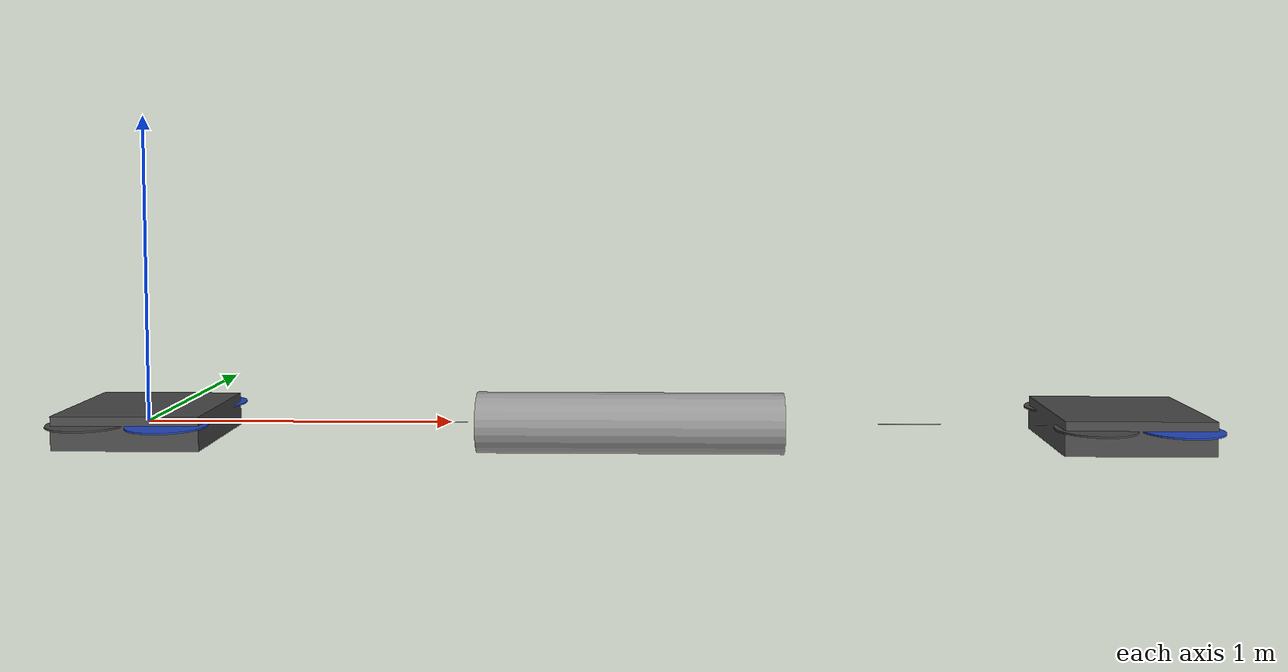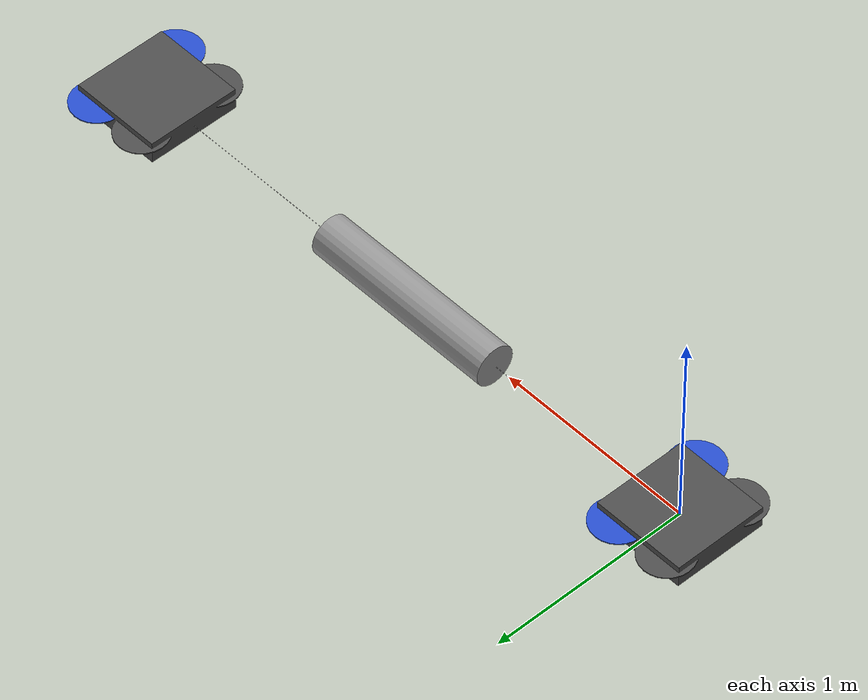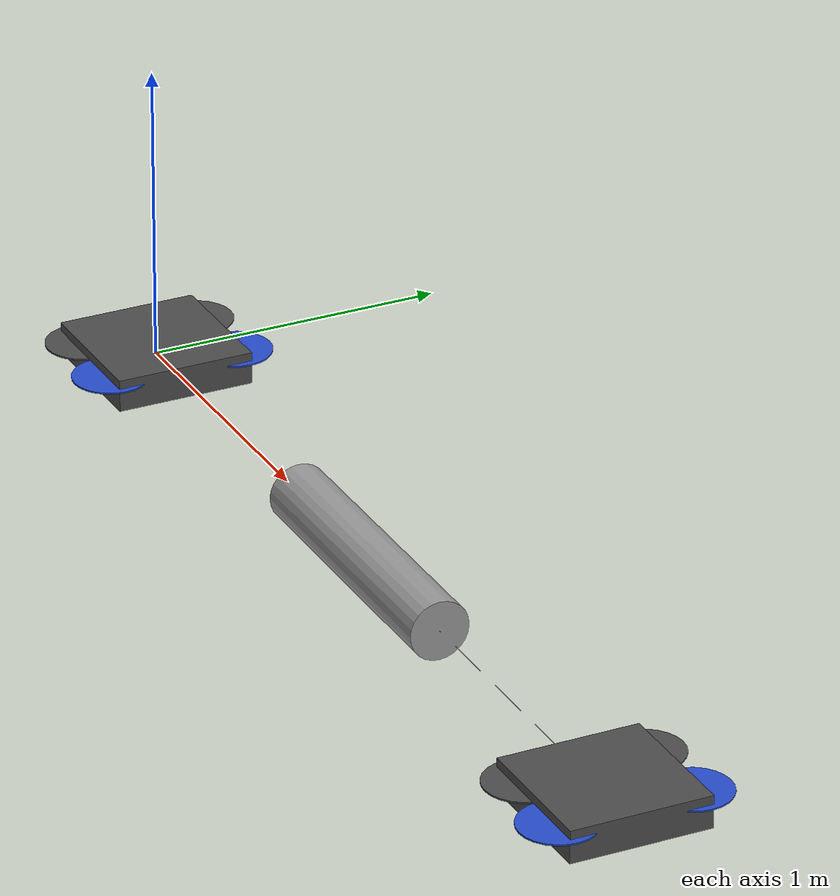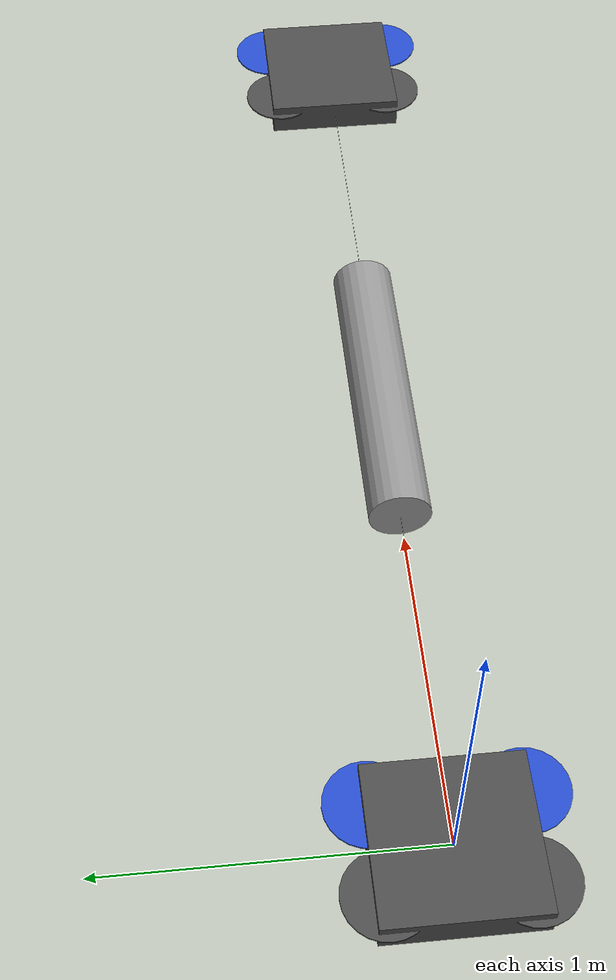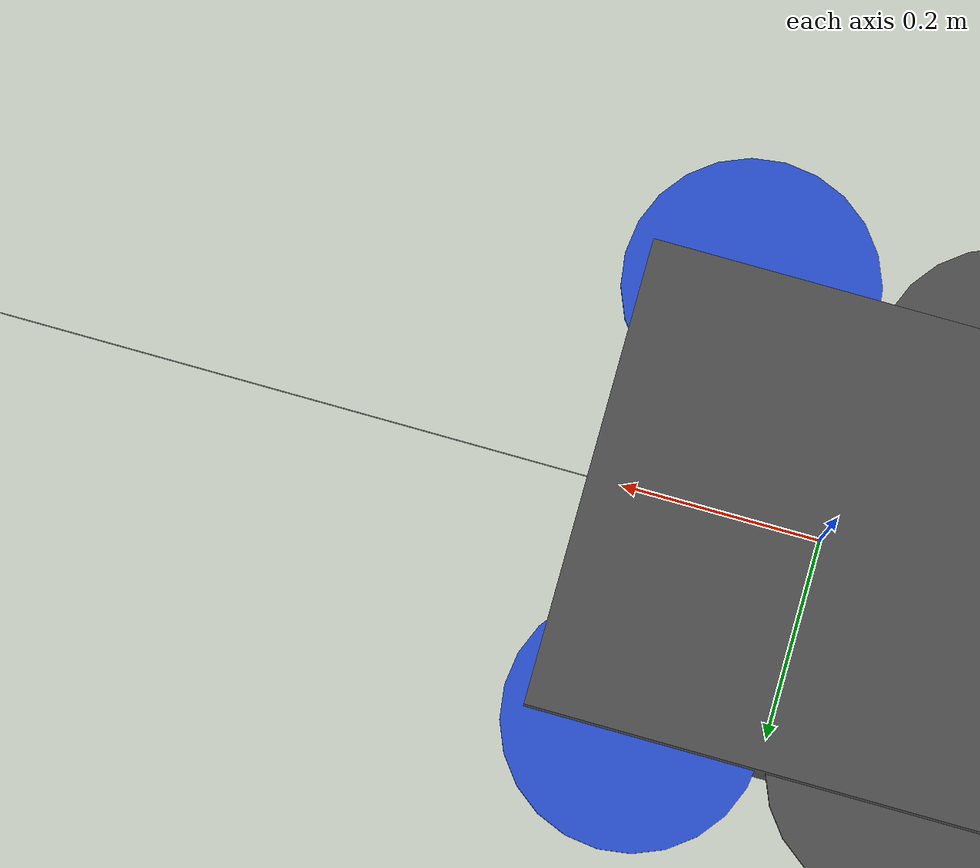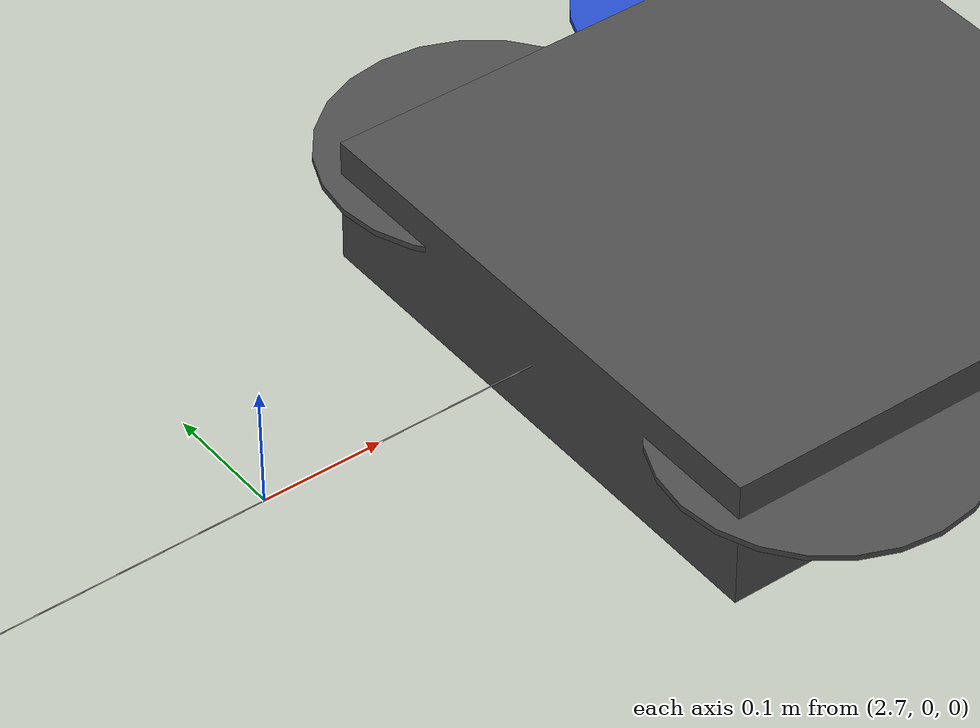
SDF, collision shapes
<?xml version='1.0'?>
<sdf version='1.6'>
  <model name='default'>
    <model name='iris_0'>
      <pose frame=''>0.0 0 0 0 -0 0</pose>
      <link name='base_link'>
        <pose frame=''>0 0 0 0 -0 0</pose>
        <inertial>
          <pose frame=''>0 0 0 0 -0 0</pose>
          <mass>1.5</mass>
          <inertia>
            <ixx>0.0347563</ixx>
            <ixy>0</ixy>
            <ixz>0</ixz>
            <iyy>0.0458929</iyy>
            <iyz>0</iyz>
            <izz>0.0977</izz>
          </inertia>
        </inertial>
        <collision name='base_link_inertia_collision'>
          <pose frame=''>0 0 0 0 -0 0</pose>
          <geometry>
            <box>
              <size>0.47 0.47 0.11</size>
            </box>
          </geometry>
          <surface>
            <contact>
              <ode>
                <min_depth>0.001</min_depth>
                <max_vel>0</max_vel>
              </ode>
            </contact>
            <friction>
              <ode/>
            </friction>
          </surface>
        </collision>
        <visual name='base_link_inertia_visual'>
          <pose frame=''>0 0 0 0 -0 0</pose>
          <geometry>
            <mesh>
              <scale>1 1 1</scale>
              <uri>model://rotors_description/meshes/iris.stl</uri>
            </mesh>
          </geometry>
          <material>
            <script>
              <name>Gazebo/DarkGrey</name>
              <uri>file://media/materials/scripts/gazebo.material</uri>
            </script>
          </material>
        </visual>
        <gravity>1</gravity>
        <velocity_decay/>
        <self_collide>0</self_collide>
      </link>
      <link name='/imu_link'>
        <pose frame=''>0 0 0 0 -0 0</pose>
        <inertial>
          <pose frame=''>0 0 0 0 -0 0</pose>
          <mass>0.015</mass>
          <inertia>
            <ixx>1e-05</ixx>
            <ixy>0</ixy>
            <ixz>0</ixz>
            <iyy>1e-05</iyy>
            <iyz>0</iyz>
            <izz>1e-05</izz>
          </inertia>
        </inertial>
      </link>
      <joint name='/imu_joint' type='revolute'>
        <child>/imu_link</child>
        <parent>base_link</parent>
        <axis>
          <xyz>1 0 0</xyz>
          <limit>
            <lower>0</lower>
            <upper>0</upper>
            <effort>0</effort>
            <velocity>0</velocity>
          </limit>
          <dynamics>
            <spring_reference>0</spring_reference>
            <spring_stiffness>0</spring_stiffness>
          </dynamics>
          <use_parent_model_frame>1</use_parent_model_frame>
        </axis>
      </joint>
      <link name='rotor_0'>
        <pose frame=''>0.13 -0.22 0.023 0 -0 0</pose>
        <inertial>
          <pose frame=''>0 0 0 0 -0 0</pose>
          <mass>0.005</mass>
          <inertia>
            <ixx>9.75e-07</ixx>
            <ixy>0</ixy>
            <ixz>0</ixz>
            <iyy>0.000273104</iyy>
            <iyz>0</iyz>
            <izz>0.000274004</izz>
          </inertia>
        </inertial>
        <collision name='rotor_0_collision'>
          <pose frame=''>0 0 0 0 -0 0</pose>
          <geometry>
            <cylinder>
              <length>0.005</length>
              <radius>0.128</radius>
            </cylinder>
          </geometry>
          <surface>
            <contact>
              <ode/>
            </contact>
            <friction>
              <ode/>
            </friction>
          </surface>
        </collision>
        <visual name='rotor_0_visual'>
          <pose frame=''>0 0 0 0 -0 0</pose>
          <geometry>
            <mesh>
              <scale>1 1 1</scale>
              <uri>model://rotors_description/meshes/iris_prop_ccw.dae</uri>
            </mesh>
          </geometry>
          <material>
            <script>
              <name>Gazebo/Blue</name>
              <uri>file://media/materials/scripts/gazebo.material</uri>
            </script>
          </material>
        </visual>
        <gravity>1</gravity>
        <velocity_decay/>
        <self_collide>0</self_collide>
      </link>
      <joint name='rotor_0_joint' type='revolute'>
        <child>rotor_0</child>
        <parent>base_link</parent>
        <axis>
          <xyz>0 0 1</xyz>
          <limit>
            <lower>-1e+16</lower>
            <upper>1e+16</upper>
          </limit>
          <dynamics>
            <spring_reference>0</spring_reference>
            <spring_stiffness>0</spring_stiffness>
          </dynamics>
          <use_parent_model_frame>1</use_parent_model_frame>
        </axis>
      </joint>
      <link name='rotor_1'>
        <pose frame=''>-0.13 0.2 0.023 0 -0 0</pose>
        <inertial>
          <pose frame=''>0 0 0 0 -0 0</pose>
          <mass>0.005</mass>
          <inertia>
            <ixx>9.75e-07</ixx>
            <ixy>0</ixy>
            <ixz>0</ixz>
            <iyy>0.000273104</iyy>
            <iyz>0</iyz>
            <izz>0.000274004</izz>
          </inertia>
        </inertial>
        <collision name='rotor_1_collision'>
          <pose frame=''>0 0 0 0 -0 0</pose>
          <geometry>
            <cylinder>
              <length>0.005</length>
              <radius>0.128</radius>
            </cylinder>
          </geometry>
          <surface>
            <contact>
              <ode/>
            </contact>
            <friction>
              <ode/>
            </friction>
          </surface>
        </collision>
        <visual name='rotor_1_visual'>
          <pose frame=''>0 0 0 0 -0 0</pose>
          <geometry>
            <mesh>
              <scale>1 1 1</scale>
              <uri>model://rotors_description/meshes/iris_prop_ccw.dae</uri>
            </mesh>
          </geometry>
          <material>
            <script>
              <name>Gazebo/DarkGrey</name>
              <uri>file://media/materials/scripts/gazebo.material</uri>
            </script>
          </material>
        </visual>
        <gravity>1</gravity>
        <velocity_decay/>
        <self_collide>0</self_collide>
      </link>
      <joint name='rotor_1_joint' type='revolute'>
        <child>rotor_1</child>
        <parent>base_link</parent>
        <axis>
          <xyz>0 0 1</xyz>
          <limit>
            <lower>-1e+16</lower>
            <upper>1e+16</upper>
          </limit>
          <dynamics>
            <spring_reference>0</spring_reference>
            <spring_stiffness>0</spring_stiffness>
          </dynamics>
          <use_parent_model_frame>1</use_parent_model_frame>
        </axis>
      </joint>
      <link name='rotor_2'>
        <pose frame=''>0.13 0.22 0.023 0 -0 0</pose>
        <inertial>
          <pose frame=''>0 0 0 0 -0 0</pose>
          <mass>0.005</mass>
          <inertia>
            <ixx>9.75e-07</ixx>
            <ixy>0</ixy>
            <ixz>0</ixz>
            <iyy>0.000273104</iyy>
            <iyz>0</iyz>
            <izz>0.000274004</izz>
          </inertia>
        </inertial>
        <collision name='rotor_2_collision'>
          <pose frame=''>0 0 0 0 -0 0</pose>
          <geometry>
            <cylinder>
              <length>0.005</length>
              <radius>0.128</radius>
            </cylinder>
          </geometry>
          <surface>
            <contact>
              <ode/>
            </contact>
            <friction>
              <ode/>
            </friction>
          </surface>
        </collision>
        <visual name='rotor_2_visual'>
          <pose frame=''>0 0 0 0 -0 0</pose>
          <geometry>
            <mesh>
              <scale>1 1 1</scale>
              <uri>model://rotors_description/meshes/iris_prop_cw.dae</uri>
            </mesh>
          </geometry>
          <material>
            <script>
              <name>Gazebo/Blue</name>
              <uri>file://media/materials/scripts/gazebo.material</uri>
            </script>
          </material>
        </visual>
        <gravity>1</gravity>
        <velocity_decay/>
        <self_collide>0</self_collide>
      </link>
      <joint name='rotor_2_joint' type='revolute'>
        <child>rotor_2</child>
        <parent>base_link</parent>
        <axis>
          <xyz>0 0 1</xyz>
          <limit>
            <lower>-1e+16</lower>
            <upper>1e+16</upper>
          </limit>
          <dynamics>
            <spring_reference>0</spring_reference>
            <spring_stiffness>0</spring_stiffness>
          </dynamics>
          <use_parent_model_frame>1</use_parent_model_frame>
        </axis>
      </joint>
      <link name='rotor_3'>
        <pose frame=''>-0.13 -0.2 0.023 0 -0 0</pose>
        <inertial>
          <pose frame=''>0 0 0 0 -0 0</pose>
          <mass>0.005</mass>
          <inertia>
            <ixx>9.75e-07</ixx>
            <ixy>0</ixy>
            <ixz>0</ixz>
            <iyy>0.000273104</iyy>
            <iyz>0</iyz>
            <izz>0.000274004</izz>
          </inertia>
        </inertial>
        <collision name='rotor_3_collision'>
          <pose frame=''>0 0 0 0 -0 0</pose>
          <geometry>
            <cylinder>
              <length>0.005</length>
              <radius>0.128</radius>
            </cylinder>
          </geometry>
          <surface>
            <contact>
              <ode/>
            </contact>
            <friction>
              <ode/>
            </friction>
          </surface>
        </collision>
        <visual name='rotor_3_visual'>
          <pose frame=''>0 0 0 0 -0 0</pose>
          <geometry>
            <mesh>
              <scale>1 1 1</scale>
              <uri>model://rotors_description/meshes/iris_prop_cw.dae</uri>
            </mesh>
          </geometry>
          <material>
            <script>
              <name>Gazebo/DarkGrey</name>
              <uri>file://media/materials/scripts/gazebo.material</uri>
            </script>
          </material>
        </visual>
        <gravity>1</gravity>
        <velocity_decay/>
        <self_collide>0</self_collide>
      </link>
      <joint name='rotor_3_joint' type='revolute'>
        <child>rotor_3</child>
        <parent>base_link</parent>
        <axis>
          <xyz>0 0 1</xyz>
          <limit>
            <lower>-1e+16</lower>
            <upper>1e+16</upper>
          </limit>
          <dynamics>
            <spring_reference>0</spring_reference>
            <spring_stiffness>0</spring_stiffness>
          </dynamics>
          <use_parent_model_frame>1</use_parent_model_frame>
        </axis>
      </joint>
      <link name='big_link_a0'>
        <pose frame=''>0.385 0 0 0 1.57079 0</pose>
        <inertial>
          <mass>0.04</mass>
          <inertia>
            <ixx>0.00333333</ixx>
            <ixy>0</ixy>
            <ixz>0</ixz>
            <iyy>0.00333333</iyy>
            <iyz>0</iyz>
            <izz>0</izz>
          </inertia>
          <pose frame=''>0 0 0 0 -0 0</pose>
        </inertial>
        <self_collide>0</self_collide>
        <kinematic>0</kinematic>
        <gravity>1</gravity>
        <visual name='visual'>
          <pose frame=''>0 0 0 0 -0 0</pose>
          <geometry>
            <cylinder>
              <radius>0.0005</radius>
              <length>0.2</length>
            </cylinder>
          </geometry>
          <material>
            <lighting>1</lighting>
            <script>
              <uri>file://media/materials/scripts/gazebo.material</uri>
              <name>Gazebo/Grey</name>
            </script>
            <ambient>0.3 0.3 0.3 1</ambient>
            <diffuse>0.7 0.7 0.7 1</diffuse>
            <specular>0.01 0.01 0.01 1</specular>
            <emissive>0 0 0 1</emissive>
            <shader type='vertex'>
              <normal_map>__default__</normal_map>
            </shader>
          </material>
          <cast_shadows>1</cast_shadows>
          <transparency>0</transparency>
        </visual>
        <collision name='collision'>
          <laser_retro>0</laser_retro>
          <max_contacts>10</max_contacts>
          <pose frame=''>0 0 0 0 -0 0</pose>
          <geometry>
            <cylinder>
              <radius>0.0005</radius>
              <length>0.2</length>
            </cylinder>
          </geometry>
          <surface>
            <friction>
              <ode>
                <mu>1</mu>
                <mu2>1</mu2>
                <fdir1>0 0 0</fdir1>
                <slip1>0</slip1>
                <slip2>0</slip2>
              </ode>
              <torsional>
                <coefficient>1</coefficient>
                <patch_radius>0</patch_radius>
                <surface_radius>0</surface_radius>
                <use_patch_radius>1</use_patch_radius>
                <ode>
                  <slip>0</slip>
                </ode>
              </torsional>
            </friction>
            <bounce>
              <restitution_coefficient>0</restitution_coefficient>
              <threshold>1e+06</threshold>
            </bounce>
            <contact>
              <collide_without_contact>0</collide_without_contact>
              <collide_without_contact_bitmask>1</collide_without_contact_bitmask>
              <collide_bitmask>1</collide_bitmask>
              <ode>
                <soft_cfm>0</soft_cfm>
                <soft_erp>0.2</soft_erp>
                <kp>1e+13</kp>
                <kd>1</kd>
                <max_vel>0.01</max_vel>
                <min_depth>0</min_depth>
              </ode>
              <bullet>
                <split_impulse>1</split_impulse>
                <split_impulse_penetration_threshold>-0.01</split_impulse_penetration_threshold>
                <soft_cfm>0</soft_cfm>
                <soft_erp>0.2</soft_erp>
                <kp>1e+13</kp>
                <kd>1</kd>
              </bullet>
            </contact>
          </surface>
        </collision>
      </link>
      <link name='big_link_a1'>
        <pose frame=''>0.585 0 1e-06 0 1.57079 0</pose>
        <inertial>
          <mass>0.04</mass>
          <inertia>
            <ixx>0.00333333</ixx>
            <ixy>0</ixy>
            <ixz>0</ixz>
            <iyy>0.00333333</iyy>
            <iyz>0</iyz>
            <izz>0</izz>
          </inertia>
          <pose frame=''>0 0 0 0 -0 0</pose>
        </inertial>
        <self_collide>0</self_collide>
        <kinematic>0</kinematic>
        <gravity>1</gravity>
        <visual name='visual'>
          <pose frame=''>0 0 0 0 -0 0</pose>
          <geometry>
            <cylinder>
              <radius>0.0005</radius>
              <length>0.2</length>
            </cylinder>
          </geometry>
          <material>
            <lighting>1</lighting>
            <script>
              <uri>file://media/materials/scripts/gazebo.material</uri>
              <name>Gazebo/Grey</name>
            </script>
            <ambient>0.3 0.3 0.3 1</ambient>
            <diffuse>0.7 0.7 0.7 1</diffuse>
            <specular>0.01 0.01 0.01 1</specular>
            <emissive>0 0 0 1</emissive>
            <shader type='vertex'>
              <normal_map>__default__</normal_map>
            </shader>
          </material>
          <cast_shadows>1</cast_shadows>
          <transparency>0</transparency>
        </visual>
        <collision name='collision'>
          <laser_retro>0</laser_retro>
          <max_contacts>10</max_contacts>
          <pose frame=''>0 0 0 0 -0 0</pose>
          <geometry>
            <cylinder>
              <radius>0.0005</radius>
              <length>0.2</length>
            </cylinder>
          </geometry>
          <surface>
            <friction>
              <ode>
                <mu>1</mu>
                <mu2>1</mu2>
                <fdir1>0 0 0</fdir1>
                <slip1>0</slip1>
                <slip2>0</slip2>
              </ode>
              <torsional>
                <coefficient>1</coefficient>
                <patch_radius>0</patch_radius>
                <surface_radius>0</surface_radius>
                <use_patch_radius>1</use_patch_radius>
                <ode>
                  <slip>0</slip>
                </ode>
              </torsional>
            </friction>
            <bounce>
              <restitution_coefficient>0</restitution_coefficient>
              <threshold>1e+06</threshold>
            </bounce>
            <contact>
              <collide_without_contact>0</collide_without_contact>
              <collide_without_contact_bitmask>1</collide_without_contact_bitmask>
              <collide_bitmask>1</collide_bitmask>
              <ode>
                <soft_cfm>0</soft_cfm>
                <soft_erp>0.2</soft_erp>
                <kp>1e+13</kp>
                <kd>1</kd>
                <max_vel>0.01</max_vel>
                <min_depth>0</min_depth>
              </ode>
              <bullet>
                <split_impulse>1</split_impulse>
                <split_impulse_penetration_threshold>-0.01</split_impulse_penetration_threshold>
                <soft_cfm>0</soft_cfm>
                <soft_erp>0.2</soft_erp>
                <kp>1e+13</kp>
                <kd>1</kd>
              </bullet>
            </contact>
          </surface>
        </collision>
      </link>
      <link name='big_link_a2'>
        <pose frame=''>0.785 0 3e-06 0 1.57079 0</pose>
        <inertial>
          <mass>0.04</mass>
          <inertia>
            <ixx>0.00333333</ixx>
            <ixy>0</ixy>
            <ixz>0</ixz>
            <iyy>0.00333333</iyy>
            <iyz>0</iyz>
            <izz>0</izz>
          </inertia>
          <pose frame=''>0 0 0 0 -0 0</pose>
        </inertial>
        <self_collide>0</self_collide>
        <kinematic>0</kinematic>
        <gravity>1</gravity>
        <visual name='visual'>
          <pose frame=''>0 0 0 0 -0 0</pose>
          <geometry>
            <cylinder>
              <radius>0.0005</radius>
              <length>0.2</length>
            </cylinder>
          </geometry>
          <material>
            <lighting>1</lighting>
            <script>
              <uri>file://media/materials/scripts/gazebo.material</uri>
              <name>Gazebo/Grey</name>
            </script>
            <ambient>0.3 0.3 0.3 1</ambient>
            <diffuse>0.7 0.7 0.7 1</diffuse>
            <specular>0.01 0.01 0.01 1</specular>
            <emissive>0 0 0 1</emissive>
            <shader type='vertex'>
              <normal_map>__default__</normal_map>
            </shader>
          </material>
          <cast_shadows>1</cast_shadows>
          <transparency>0</transparency>
        </visual>
        <collision name='collision'>
          <laser_retro>0</laser_retro>
          <max_contacts>10</max_contacts>
          <pose frame=''>0 0 0 0 -0 0</pose>
          <geometry>
            <cylinder>
              <radius>0.0005</radius>
              <length>0.2</length>
            </cylinder>
          </geometry>
          <surface>
            <friction>
              <ode>
                <mu>1</mu>
                <mu2>1</mu2>
                <fdir1>0 0 0</fdir1>
                <slip1>0</slip1>
                <slip2>0</slip2>
              </ode>
              <torsional>
                <coefficient>1</coefficient>
                <patch_radius>0</patch_radius>
                <surface_radius>0</surface_radius>
                <use_patch_radius>1</use_patch_radius>
                <ode>
                  <slip>0</slip>
                </ode>
              </torsional>
            </friction>
            <bounce>
              <restitution_coefficient>0</restitution_coefficient>
              <threshold>1e+06</threshold>
            </bounce>
            <contact>
              <collide_without_contact>0</collide_without_contact>
              <collide_without_contact_bitmask>1</collide_without_contact_bitmask>
              <collide_bitmask>1</collide_bitmask>
              <ode>
                <soft_cfm>0</soft_cfm>
                <soft_erp>0.2</soft_erp>
                <kp>1e+13</kp>
                <kd>1</kd>
                <max_vel>0.01</max_vel>
                <min_depth>0</min_depth>
              </ode>
              <bullet>
                <split_impulse>1</split_impulse>
                <split_impulse_penetration_threshold>-0.01</split_impulse_penetration_threshold>
                <soft_cfm>0</soft_cfm>
                <soft_erp>0.2</soft_erp>
                <kp>1e+13</kp>
                <kd>1</kd>
              </bullet>
            </contact>
          </surface>
        </collision>
      </link>
      <link name='big_link_a3'>
        <pose frame=''>0.985 0 0 0 1.57079 0</pose>
        <inertial>
          <mass>0.04</mass>
          <inertia>
            <ixx>0.00333333</ixx>
            <ixy>0</ixy>
            <ixz>0</ixz>
            <iyy>0.00333333</iyy>
            <iyz>0</iyz>
            <izz>0</izz>
          </inertia>
          <pose frame=''>0 0 0 0 -0 0</pose>
        </inertial>
        <self_collide>0</self_collide>
        <kinematic>0</kinematic>
        <gravity>1</gravity>
        <visual name='visual'>
          <pose frame=''>0 0 0 0 -0 0</pose>
          <geometry>
            <cylinder>
              <radius>0.0005</radius>
              <length>0.2</length>
            </cylinder>
          </geometry>
          <material>
            <lighting>1</lighting>
            <script>
              <uri>file://media/materials/scripts/gazebo.material</uri>
              <name>Gazebo/Grey</name>
            </script>
            <ambient>0.3 0.3 0.3 1</ambient>
            <diffuse>0.7 0.7 0.7 1</diffuse>
            <specular>0.01 0.01 0.01 1</specular>
            <emissive>0 0 0 1</emissive>
            <shader type='vertex'>
              <normal_map>__default__</normal_map>
            </shader>
          </material>
          <cast_shadows>1</cast_shadows>
          <transparency>0</transparency>
        </visual>
        <collision name='collision'>
          <laser_retro>0</laser_retro>
          <max_contacts>10</max_contacts>
          <pose frame=''>0 0 0 0 -0 0</pose>
          <geometry>
            <cylinder>
              <radius>0.0005</radius>
              <length>0.2</length>
            </cylinder>
          </geometry>
          <surface>
            <friction>
              <ode>
                <mu>1</mu>
                <mu2>1</mu2>
                <fdir1>0 0 0</fdir1>
                <slip1>0</slip1>
                <slip2>0</slip2>
              </ode>
              <torsional>
                <coefficient>1</coefficient>
                <patch_radius>0</patch_radius>
                <surface_radius>0</surface_radius>
                <use_patch_radius>1</use_patch_radius>
                <ode>
                  <slip>0</slip>
                </ode>
              </torsional>
            </friction>
            <bounce>
              <restitution_coefficient>0</restitution_coefficient>
              <threshold>1e+06</threshold>
            </bounce>
            <contact>
              <collide_without_contact>0</collide_without_contact>
              <collide_without_contact_bitmask>1</collide_without_contact_bitmask>
              <collide_bitmask>1</collide_bitmask>
              <ode>
                <soft_cfm>0</soft_cfm>
                <soft_erp>0.2</soft_erp>
                <kp>1e+13</kp>
                <kd>1</kd>
                <max_vel>0.01</max_vel>
                <min_depth>0</min_depth>
              </ode>
              <bullet>
                <split_impulse>1</split_impulse>
                <split_impulse_penetration_threshold>-0.01</split_impulse_penetration_threshold>
                <soft_cfm>0</soft_cfm>
                <soft_erp>0.2</soft_erp>
                <kp>1e+13</kp>
                <kd>1</kd>
              </bullet>
            </contact>
          </surface>
        </collision>
      </link>
      <link name='small_link_a0'>
        <pose frame=''>0.24 0 0 0 1.57079 0</pose>
        <inertial>
          <mass>0.002</mass>
          <inertia>
            <ixx>2e-08</ixx>
            <ixy>0</ixy>
            <ixz>0</ixz>
            <iyy>0</iyy>
            <iyz>0</iyz>
            <izz>2e-08</izz>
          </inertia>
          <pose frame=''>0 0 0 0 -0 0</pose>
        </inertial>
        <self_collide>0</self_collide>
        <kinematic>0</kinematic>
        <gravity>1</gravity>
        <visual name='visual'>
          <pose frame=''>0 0 0 0 -0 0</pose>
          <geometry>
            <cylinder>
              <radius>0.0005</radius>
              <length>0.01</length>
            </cylinder>
          </geometry>
          <material>
            <lighting>1</lighting>
            <script>
              <uri>file://media/materials/scripts/gazebo.material</uri>
              <name>Gazebo/Grey</name>
            </script>
            <ambient>0.3 0.3 0.3 1</ambient>
            <diffuse>0.7 0.7 0.7 1</diffuse>
            <specular>0.01 0.01 0.01 1</specular>
            <emissive>0 0 0 1</emissive>
            <shader type='vertex'>
              <normal_map>__default__</normal_map>
            </shader>
          </material>
          <cast_shadows>1</cast_shadows>
          <transparency>0</transparency>
        </visual>
        <collision name='collision'>
          <laser_retro>0</laser_retro>
          <max_contacts>10</max_contacts>
          <pose frame=''>0 0 0 0 -0 0</pose>
          <geometry>
            <cylinder>
              <radius>0.0005</radius>
              <length>0.01</length>
            </cylinder>
          </geometry>
          <surface>
            <friction>
              <ode>
                <mu>1</mu>
                <mu2>1</mu2>
                <fdir1>0 0 0</fdir1>
                <slip1>0</slip1>
                <slip2>0</slip2>
              </ode>
              <torsional>
                <coefficient>1</coefficient>
                <patch_radius>0</patch_radius>
                <surface_radius>0</surface_radius>
                <use_patch_radius>1</use_patch_radius>
                <ode>
                  <slip>0</slip>
                </ode>
              </torsional>
            </friction>
            <bounce>
              <restitution_coefficient>0</restitution_coefficient>
              <threshold>1e+06</threshold>
            </bounce>
            <contact>
              <collide_without_contact>0</collide_without_contact>
              <collide_without_contact_bitmask>1</collide_without_contact_bitmask>
              <collide_bitmask>1</collide_bitmask>
              <ode>
                <soft_cfm>0</soft_cfm>
                <soft_erp>0.2</soft_erp>
                <kp>1e+13</kp>
                <kd>1</kd>
                <max_vel>0.01</max_vel>
                <min_depth>0</min_depth>
              </ode>
              <bullet>
                <split_impulse>1</split_impulse>
                <split_impulse_penetration_threshold>-0.01</split_impulse_penetration_threshold>
                <soft_cfm>0</soft_cfm>
                <soft_erp>0.2</soft_erp>
                <kp>1e+13</kp>
                <kd>1</kd>
              </bullet>
            </contact>
          </surface>
        </collision>
      </link>
      <link name='small_link_a1'>
        <pose frame=''>0.25 0 0 0 1.57079 0</pose>
        <inertial>
          <mass>0.002</mass>
          <inertia>
            <ixx>2e-08</ixx>
            <ixy>0</ixy>
            <ixz>0</ixz>
            <iyy>0</iyy>
            <iyz>0</iyz>
            <izz>2e-08</izz>
          </inertia>
          <pose frame=''>0 0 0 0 -0 0</pose>
        </inertial>
        <self_collide>0</self_collide>
        <kinematic>0</kinematic>
        <gravity>1</gravity>
        <visual name='visual'>
          <pose frame=''>0 0 0 0 -0 0</pose>
          <geometry>
            <cylinder>
              <radius>0.0005</radius>
              <length>0.01</length>
            </cylinder>
          </geometry>
          <material>
            <lighting>1</lighting>
            <script>
              <uri>file://media/materials/scripts/gazebo.material</uri>
              <name>Gazebo/Grey</name>
            </script>
            <ambient>0.3 0.3 0.3 1</ambient>
            <diffuse>0.7 0.7 0.7 1</diffuse>
            <specular>0.01 0.01 0.01 1</specular>
            <emissive>0 0 0 1</emissive>
            <shader type='vertex'>
              <normal_map>__default__</normal_map>
            </shader>
          </material>
          <cast_shadows>1</cast_shadows>
          <transparency>0</transparency>
        </visual>
        <collision name='collision'>
          <laser_retro>0</laser_retro>
          <max_contacts>10</max_contacts>
          <pose frame=''>0 0 0 0 -0 0</pose>
          <geometry>
            <cylinder>
              <radius>0.0005</radius>
              <length>0.01</length>
            </cylinder>
          </geometry>
          <surface>
            <friction>
              <ode>
                <mu>1</mu>
                <mu2>1</mu2>
                <fdir1>0 0 0</fdir1>
                <slip1>0</slip1>
                <slip2>0</slip2>
              </ode>
              <torsional>
                <coefficient>1</coefficient>
                <patch_radius>0</patch_radius>
                <surface_radius>0</surface_radius>
                <use_patch_radius>1</use_patch_radius>
                <ode>
                  <slip>0</slip>
                </ode>
              </torsional>
            </friction>
            <bounce>
              <restitution_coefficient>0</restitution_coefficient>
              <threshold>1e+06</threshold>
            </bounce>
            <contact>
              <collide_without_contact>0</collide_without_contact>
              <collide_without_contact_bitmask>1</collide_without_contact_bitmask>
              <collide_bitmask>1</collide_bitmask>
              <ode>
                <soft_cfm>0</soft_cfm>
                <soft_erp>0.2</soft_erp>
                <kp>1e+13</kp>
                <kd>1</kd>
                <max_vel>0.01</max_vel>
                <min_depth>0</min_depth>
              </ode>
              <bullet>
                <split_impulse>1</split_impulse>
                <split_impulse_penetration_threshold>-0.01</split_impulse_penetration_threshold>
                <soft_cfm>0</soft_cfm>
                <soft_erp>0.2</soft_erp>
                <kp>1e+13</kp>
                <kd>1</kd>
              </bullet>
            </contact>
          </surface>
        </collision>
      </link>
      <link name='small_link_a2'>
        <pose frame=''>0.26 0 0 0 1.57079 0</pose>
        <inertial>
          <mass>0.002</mass>
          <inertia>
            <ixx>2e-08</ixx>
            <ixy>0</ixy>
            <ixz>0</ixz>
            <iyy>0</iyy>
            <iyz>0</iyz>
            <izz>2e-08</izz>
          </inertia>
          <pose frame=''>0 0 0 0 -0 0</pose>
        </inertial>
        <self_collide>0</self_collide>
        <kinematic>0</kinematic>
        <gravity>1</gravity>
        <visual name='visual'>
          <pose frame=''>0 0 0 0 -0 0</pose>
          <geometry>
            <cylinder>
              <radius>0.0005</radius>
              <length>0.01</length>
            </cylinder>
          </geometry>
          <material>
            <lighting>1</lighting>
            <script>
              <uri>file://media/materials/scripts/gazebo.material</uri>
              <name>Gazebo/Grey</name>
            </script>
            <ambient>0.3 0.3 0.3 1</ambient>
            <diffuse>0.7 0.7 0.7 1</diffuse>
            <specular>0.01 0.01 0.01 1</specular>
            <emissive>0 0 0 1</emissive>
            <shader type='vertex'>
              <normal_map>__default__</normal_map>
            </shader>
          </material>
          <cast_shadows>1</cast_shadows>
          <transparency>0</transparency>
        </visual>
        <collision name='collision'>
          <laser_retro>0</laser_retro>
          <max_contacts>10</max_contacts>
          <pose frame=''>0 0 0 0 -0 0</pose>
          <geometry>
            <cylinder>
              <radius>0.0005</radius>
              <length>0.01</length>
            </cylinder>
          </geometry>
          <surface>
            <friction>
              <ode>
                <mu>1</mu>
                <mu2>1</mu2>
                <fdir1>0 0 0</fdir1>
                <slip1>0</slip1>
                <slip2>0</slip2>
              </ode>
              <torsional>
                <coefficient>1</coefficient>
                <patch_radius>0</patch_radius>
                <surface_radius>0</surface_radius>
                <use_patch_radius>1</use_patch_radius>
                <ode>
                  <slip>0</slip>
                </ode>
              </torsional>
            </friction>
            <bounce>
              <restitution_coefficient>0</restitution_coefficient>
              <threshold>1e+06</threshold>
            </bounce>
            <contact>
              <collide_without_contact>0</collide_without_contact>
              <collide_without_contact_bitmask>1</collide_without_contact_bitmask>
              <collide_bitmask>1</collide_bitmask>
              <ode>
                <soft_cfm>0</soft_cfm>
                <soft_erp>0.2</soft_erp>
                <kp>1e+13</kp>
                <kd>1</kd>
                <max_vel>0.01</max_vel>
                <min_depth>0</min_depth>
              </ode>
              <bullet>
                <split_impulse>1</split_impulse>
                <split_impulse_penetration_threshold>-0.01</split_impulse_penetration_threshold>
                <soft_cfm>0</soft_cfm>
                <soft_erp>0.2</soft_erp>
                <kp>1e+13</kp>
                <kd>1</kd>
              </bullet>
            </contact>
          </surface>
        </collision>
      </link>
      <link name='small_link_a3'>
        <pose frame=''>0.27 0 0 0 1.57079 0</pose>
        <inertial>
          <mass>0.002</mass>
          <inertia>
            <ixx>2e-08</ixx>
            <ixy>0</ixy>
            <ixz>0</ixz>
            <iyy>0</iyy>
            <iyz>0</iyz>
            <izz>2e-08</izz>
          </inertia>
          <pose frame=''>0 0 0 0 -0 0</pose>
        </inertial>
        <self_collide>0</self_collide>
        <kinematic>0</kinematic>
        <gravity>1</gravity>
        <visual name='visual'>
          <pose frame=''>0 0 0 0 -0 0</pose>
          <geometry>
            <cylinder>
              <radius>0.0005</radius>
              <length>0.01</length>
            </cylinder>
          </geometry>
          <material>
            <lighting>1</lighting>
            <script>
              <uri>file://media/materials/scripts/gazebo.material</uri>
              <name>Gazebo/Grey</name>
            </script>
            <ambient>0.3 0.3 0.3 1</ambient>
            <diffuse>0.7 0.7 0.7 1</diffuse>
            <specular>0.01 0.01 0.01 1</specular>
            <emissive>0 0 0 1</emissive>
            <shader type='vertex'>
              <normal_map>__default__</normal_map>
            </shader>
          </material>
          <cast_shadows>1</cast_shadows>
          <transparency>0</transparency>
        </visual>
        <collision name='collision'>
          <laser_retro>0</laser_retro>
          <max_contacts>10</max_contacts>
          <pose frame=''>0 0 0 0 -0 0</pose>
          <geometry>
            <cylinder>
              <radius>0.0005</radius>
              <length>0.01</length>
            </cylinder>
          </geometry>
          <surface>
            <friction>
              <ode>
                <mu>1</mu>
                <mu2>1</mu2>
                <fdir1>0 0 0</fdir1>
                <slip1>0</slip1>
                <slip2>0</slip2>
              </ode>
              <torsional>
                <coefficient>1</coefficient>
                <patch_radius>0</patch_radius>
                <surface_radius>0</surface_radius>
                <use_patch_radius>1</use_patch_radius>
                <ode>
                  <slip>0</slip>
                </ode>
              </torsional>
            </friction>
            <bounce>
              <restitution_coefficient>0</restitution_coefficient>
              <threshold>1e+06</threshold>
            </bounce>
            <contact>
              <collide_without_contact>0</collide_without_contact>
              <collide_without_contact_bitmask>1</collide_without_contact_bitmask>
              <collide_bitmask>1</collide_bitmask>
              <ode>
                <soft_cfm>0</soft_cfm>
                <soft_erp>0.2</soft_erp>
                <kp>1e+13</kp>
                <kd>1</kd>
                <max_vel>0.01</max_vel>
                <min_depth>0</min_depth>
              </ode>
              <bullet>
                <split_impulse>1</split_impulse>
                <split_impulse_penetration_threshold>-0.01</split_impulse_penetration_threshold>
                <soft_cfm>0</soft_cfm>
                <soft_erp>0.2</soft_erp>
                <kp>1e+13</kp>
                <kd>1</kd>
              </bullet>
            </contact>
          </surface>
        </collision>
      </link>
      <link name='small_link_a4'>
        <pose frame=''>0.28 0 0 0 1.57079 0</pose>
        <inertial>
          <mass>0.002</mass>
          <inertia>
            <ixx>2e-08</ixx>
            <ixy>0</ixy>
            <ixz>0</ixz>
            <iyy>0</iyy>
            <iyz>0</iyz>
            <izz>2e-08</izz>
          </inertia>
          <pose frame=''>0 0 0 0 -0 0</pose>
        </inertial>
        <self_collide>0</self_collide>
        <kinematic>0</kinematic>
        <gravity>1</gravity>
        <visual name='visual'>
          <pose frame=''>0 0 0 0 -0 0</pose>
          <geometry>
            <cylinder>
              <radius>0.0005</radius>
              <length>0.01</length>
            </cylinder>
          </geometry>
          <material>
            <lighting>1</lighting>
            <script>
              <uri>file://media/materials/scripts/gazebo.material</uri>
              <name>Gazebo/Grey</name>
            </script>
            <ambient>0.3 0.3 0.3 1</ambient>
            <diffuse>0.7 0.7 0.7 1</diffuse>
            <specular>0.01 0.01 0.01 1</specular>
            <emissive>0 0 0 1</emissive>
            <shader type='vertex'>
              <normal_map>__default__</normal_map>
            </shader>
          </material>
          <cast_shadows>1</cast_shadows>
          <transparency>0</transparency>
        </visual>
        <collision name='collision'>
          <laser_retro>0</laser_retro>
          <max_contacts>10</max_contacts>
          <pose frame=''>0 0 0 0 -0 0</pose>
          <geometry>
            <cylinder>
              <radius>0.0005</radius>
              <length>0.01</length>
            </cylinder>
          </geometry>
          <surface>
            <friction>
              <ode>
                <mu>1</mu>
                <mu2>1</mu2>
                <fdir1>0 0 0</fdir1>
                <slip1>0</slip1>
                <slip2>0</slip2>
              </ode>
              <torsional>
                <coefficient>1</coefficient>
                <patch_radius>0</patch_radius>
                <surface_radius>0</surface_radius>
                <use_patch_radius>1</use_patch_radius>
                <ode>
                  <slip>0</slip>
                </ode>
              </torsional>
            </friction>
            <bounce>
              <restitution_coefficient>0</restitution_coefficient>
              <threshold>1e+06</threshold>
            </bounce>
            <contact>
              <collide_without_contact>0</collide_without_contact>
              <collide_without_contact_bitmask>1</collide_without_contact_bitmask>
              <collide_bitmask>1</collide_bitmask>
              <ode>
                <soft_cfm>0</soft_cfm>
                <soft_erp>0.2</soft_erp>
                <kp>1e+13</kp>
                <kd>1</kd>
                <max_vel>0.01</max_vel>
                <min_depth>0</min_depth>
              </ode>
              <bullet>
                <split_impulse>1</split_impulse>
                <split_impulse_penetration_threshold>-0.01</split_impulse_penetration_threshold>
                <soft_cfm>0</soft_cfm>
                <soft_erp>0.2</soft_erp>
                <kp>1e+13</kp>
                <kd>1</kd>
              </bullet>
            </contact>
          </surface>
        </collision>
      </link>
      <joint name='base_link_0_JOINT_0' type='ball'>
        <parent>iris_0::base_link</parent>
        <child>iris_0::small_link_a0</child>
        <pose frame=''>0 0 -0.005 0 -0 0</pose>
        <physics>
          <ode>
            <limit>
              <cfm>0</cfm>
              <erp>0.2</erp>
            </limit>
            <suspension>
              <cfm>0</cfm>
              <erp>0.2</erp>
            </suspension>
          </ode>
        </physics>
      </joint>
      <joint name='small_link_a0_JOINT_1' type='ball'>
        <parent>iris_0::small_link_a0</parent>
        <child>iris_0::small_link_a1</child>
        <pose frame=''>0 0 -0.005 0 -0 0</pose>
        <physics>
          <ode>
            <limit>
              <cfm>0</cfm>
              <erp>0.2</erp>
            </limit>
            <suspension>
              <cfm>0</cfm>
              <erp>0.2</erp>
            </suspension>
          </ode>
        </physics>
      </joint>
      <joint name='small_link_a1_JOINT_2' type='ball'>
        <parent>iris_0::small_link_a1</parent>
        <child>iris_0::small_link_a2</child>
        <pose frame=''>0 0 -0.005 0 -0 0</pose>
        <physics>
          <ode>
            <limit>
              <cfm>0</cfm>
              <erp>0.2</erp>
            </limit>
            <suspension>
              <cfm>0</cfm>
              <erp>0.2</erp>
            </suspension>
          </ode>
        </physics>
      </joint>
      <joint name='small_link_a2_JOINT_3' type='ball'>
        <parent>iris_0::small_link_a2</parent>
        <child>iris_0::small_link_a3</child>
        <pose frame=''>0 0 -0.005 0 -0 0</pose>
        <physics>
          <ode>
            <limit>
              <cfm>0</cfm>
              <erp>0.2</erp>
            </limit>
            <suspension>
              <cfm>0</cfm>
              <erp>0.2</erp>
            </suspension>
          </ode>
        </physics>
      </joint>
      <joint name='small_link_a3_JOINT_4' type='ball'>
        <parent>iris_0::small_link_a3</parent>
        <child>iris_0::small_link_a4</child>
        <pose frame=''>0 0 -0.005 0 -0 0</pose>
        <physics>
          <ode>
            <limit>
              <cfm>0</cfm>
              <erp>0.2</erp>
            </limit>
            <suspension>
              <cfm>0</cfm>
              <erp>0.2</erp>
            </suspension>
          </ode>
        </physics>
      </joint>
      <joint name='small_link_a4_JOINT_5' type='ball'>
        <parent>iris_0::small_link_a4</parent>
        <child>iris_0::big_link_a0</child>
        <pose frame=''>0 0 -0.1 0 -0 0</pose>
        <physics>
          <ode>
            <limit>
              <cfm>0</cfm>
              <erp>0.2</erp>
            </limit>
            <suspension>
              <cfm>0</cfm>
              <erp>0.2</erp>
            </suspension>
          </ode>
        </physics>
      </joint>
      <joint name='big_link_a0_JOINT_6' type='ball'>
        <parent>iris_0::big_link_a0</parent>
        <child>iris_0::big_link_a1</child>
        <pose frame=''>0 0 -0.1 0 -0 0</pose>
        <physics>
          <ode>
            <limit>
              <cfm>0</cfm>
              <erp>0.2</erp>
            </limit>
            <suspension>
              <cfm>0</cfm>
              <erp>0.2</erp>
            </suspension>
          </ode>
        </physics>
      </joint>
      <joint name='big_link_a1_JOINT_7' type='ball'>
        <parent>iris_0::big_link_a1</parent>
        <child>iris_0::big_link_a2</child>
        <pose frame=''>0 0 -0.1 0 -0 0</pose>
        <physics>
          <ode>
            <limit>
              <cfm>0</cfm>
              <erp>0.2</erp>
            </limit>
            <suspension>
              <cfm>0</cfm>
              <erp>0.2</erp>
            </suspension>
          </ode>
        </physics>
      </joint>
      <joint name='big_link_a2_JOINT_8' type='ball'>
        <parent>iris_0::big_link_a2</parent>
        <child>iris_0::big_link_a3</child>
        <pose frame=''>0 0 -0.1 0 -0 0</pose>
        <physics>
          <ode>
            <limit>
              <cfm>0</cfm>
              <erp>0.2</erp>
            </limit>
            <suspension>
              <cfm>0</cfm>
              <erp>0.2</erp>
            </suspension>
          </ode>
        </physics>
      </joint>
      <plugin name='rosbag' filename='librotors_gazebo_multirotor_base_plugin.so'>
        <robotNamespace/>
        <linkName>base_link</linkName>
        <rotorVelocitySlowdownSim>10</rotorVelocitySlowdownSim>
      </plugin>
      <plugin name='front_right_motor_model' filename='librotors_gazebo_motor_model.so'>
        <robotNamespace/>
        <jointName>rotor_0_joint</jointName>
        <linkName>rotor_0</linkName>
        <turningDirection>ccw</turningDirection>
        <timeConstantUp>0.0125</timeConstantUp>
        <timeConstantDown>0.025</timeConstantDown>
        <maxRotVelocity>1100</maxRotVelocity>
        <motorConstant>8.54858e-06</motorConstant>
        <momentConstant>0.06</momentConstant>
        <commandSubTopic>/gazebo/command/motor_speed</commandSubTopic>
        <motorNumber>0</motorNumber>
        <rotorDragCoefficient>0.000806428</rotorDragCoefficient>
        <rollingMomentCoefficient>1e-06</rollingMomentCoefficient>
        <motorSpeedPubTopic>/motor_speed/0</motorSpeedPubTopic>
        <rotorVelocitySlowdownSim>10</rotorVelocitySlowdownSim>
      </plugin>
      <plugin name='back_left_motor_model' filename='librotors_gazebo_motor_model.so'>
        <robotNamespace/>
        <jointName>rotor_1_joint</jointName>
        <linkName>rotor_1</linkName>
        <turningDirection>ccw</turningDirection>
        <timeConstantUp>0.0125</timeConstantUp>
        <timeConstantDown>0.025</timeConstantDown>
        <maxRotVelocity>1100</maxRotVelocity>
        <motorConstant>8.54858e-06</motorConstant>
        <momentConstant>0.06</momentConstant>
        <commandSubTopic>/gazebo/command/motor_speed</commandSubTopic>
        <motorNumber>1</motorNumber>
        <rotorDragCoefficient>0.000806428</rotorDragCoefficient>
        <rollingMomentCoefficient>1e-06</rollingMomentCoefficient>
        <motorSpeedPubTopic>/motor_speed/1</motorSpeedPubTopic>
        <rotorVelocitySlowdownSim>10</rotorVelocitySlowdownSim>
      </plugin>
      <plugin name='front_left_motor_model' filename='librotors_gazebo_motor_model.so'>
        <robotNamespace/>
        <jointName>rotor_2_joint</jointName>
        <linkName>rotor_2</linkName>
        <turningDirection>cw</turningDirection>
        <timeConstantUp>0.0125</timeConstantUp>
        <timeConstantDown>0.025</timeConstantDown>
        <maxRotVelocity>1100</maxRotVelocity>
        <motorConstant>8.54858e-06</motorConstant>
        <momentConstant>0.06</momentConstant>
        <commandSubTopic>/gazebo/command/motor_speed</commandSubTopic>
        <motorNumber>2</motorNumber>
        <rotorDragCoefficient>0.000806428</rotorDragCoefficient>
        <rollingMomentCoefficient>1e-06</rollingMomentCoefficient>
        <motorSpeedPubTopic>/motor_speed/2</motorSpeedPubTopic>
        <rotorVelocitySlowdownSim>10</rotorVelocitySlowdownSim>
      </plugin>
      <plugin name='back_right_motor_model' filename='librotors_gazebo_motor_model.so'>
        <robotNamespace/>
        <jointName>rotor_3_joint</jointName>
        <linkName>rotor_3</linkName>
        <turningDirection>cw</turningDirection>
        <timeConstantUp>0.0125</timeConstantUp>
        <timeConstantDown>0.025</timeConstantDown>
        <maxRotVelocity>1100</maxRotVelocity>
        <motorConstant>8.54858e-06</motorConstant>
        <momentConstant>0.06</momentConstant>
        <commandSubTopic>/gazebo/command/motor_speed</commandSubTopic>
        <motorNumber>3</motorNumber>
        <rotorDragCoefficient>0.000806428</rotorDragCoefficient>
        <rollingMomentCoefficient>1e-06</rollingMomentCoefficient>
        <motorSpeedPubTopic>/motor_speed/3</motorSpeedPubTopic>
        <rotorVelocitySlowdownSim>10</rotorVelocitySlowdownSim>
      </plugin>
      <plugin name='gps_plugin' filename='libgazebo_gps_plugin.so'>
        <robotNamespace/>
        <gpsNoise>true</gpsNoise>
      </plugin>
      <plugin name='mavlink_interface' filename='librotors_gazebo_mavlink_interface.so'>
        <robotNamespace/>
        <imuSubTopic>/imu</imuSubTopic>
        <gpsSubTopic>/gps</gpsSubTopic>
        <mavlink_addr>INADDR_ANY</mavlink_addr>
        <mavlink_udp_port>14560</mavlink_udp_port>
        <motorSpeedCommandPubTopic>/gazebo/command/motor_speed</motorSpeedCommandPubTopic>
        <control_channels>
          <channel name='rotor1'>
            <input_index>0</input_index>
            <input_offset>0</input_offset>
            <input_scaling>1000</input_scaling>
            <zero_position_disarmed>0</zero_position_disarmed>
            <zero_position_armed>100</zero_position_armed>
            <joint_control_type>velocity</joint_control_type>
          </channel>
          <channel name='rotor2'>
            <input_index>1</input_index>
            <input_offset>0</input_offset>
            <input_scaling>1000</input_scaling>
            <zero_position_disarmed>0</zero_position_disarmed>
            <zero_position_armed>100</zero_position_armed>
            <joint_control_type>velocity</joint_control_type>
          </channel>
          <channel name='rotor3'>
            <input_index>2</input_index>
            <input_offset>0</input_offset>
            <input_scaling>1000</input_scaling>
            <zero_position_disarmed>0</zero_position_disarmed>
            <zero_position_armed>100</zero_position_armed>
            <joint_control_type>velocity</joint_control_type>
          </channel>
          <channel name='rotor4'>
            <input_index>3</input_index>
            <input_offset>0</input_offset>
            <input_scaling>1000</input_scaling>
            <zero_position_disarmed>0</zero_position_disarmed>
            <zero_position_armed>100</zero_position_armed>
            <joint_control_type>velocity</joint_control_type>
          </channel>
          <channel name='rotor5'>
            <input_index>4</input_index>
            <input_offset>1</input_offset>
            <input_scaling>324.6</input_scaling>
            <zero_position_disarmed>0</zero_position_disarmed>
            <zero_position_armed>0</zero_position_armed>
            <joint_control_type>velocity</joint_control_type>
            <joint_control_pid>
              <p>0.1</p>
              <i>0</i>
              <d>0</d>
              <iMax>0.0</iMax>
              <iMin>0.0</iMin>
              <cmdMax>2</cmdMax>
              <cmdMin>-2</cmdMin>
            </joint_control_pid>
            <joint_name>zephyr_delta_wing::propeller_joint</joint_name>
          </channel>
          <channel name='rotor6'>
            <input_index>5</input_index>
            <input_offset>0</input_offset>
            <input_scaling>0.524</input_scaling>
            <zero_position_disarmed>0</zero_position_disarmed>
            <zero_position_armed>0</zero_position_armed>
            <joint_control_type>position</joint_control_type>
            <joint_name>zephyr_delta_wing::flap_left_joint</joint_name>
            <joint_control_pid>
              <p>10.0</p>
              <i>0</i>
              <d>0</d>
              <iMax>0</iMax>
              <iMin>0</iMin>
              <cmdMax>20</cmdMax>
              <cmdMin>-20</cmdMin>
            </joint_control_pid>
          </channel>
          <channel name='rotor7'>
            <input_index>6</input_index>
            <input_offset>0</input_offset>
            <input_scaling>0.524</input_scaling>
            <zero_position_disarmed>0</zero_position_disarmed>
            <zero_position_armed>0</zero_position_armed>
            <joint_control_type>position</joint_control_type>
            <joint_name>zephyr_delta_wing::flap_right_joint</joint_name>
            <joint_control_pid>
              <p>10.0</p>
              <i>0</i>
              <d>0</d>
              <iMax>0</iMax>
              <iMin>0</iMin>
              <cmdMax>20</cmdMax>
              <cmdMin>-20</cmdMin>
            </joint_control_pid>
          </channel>
          <channel name='rotor8'>
            <input_index>7</input_index>
            <input_offset>0</input_offset>
            <input_scaling>0.524</input_scaling>
            <zero_position_disarmed>0</zero_position_disarmed>
            <zero_position_armed>0</zero_position_armed>
            <joint_control_type>position</joint_control_type>
          </channel>
        </control_channels>
      </plugin>
      <static>0</static>
      <plugin name='rotors_gazebo_imu_plugin' filename='librotors_gazebo_imu_plugin.so'>
        <robotNamespace/>
        <linkName>/imu_link</linkName>
        <imuTopic>/imu</imuTopic>
        <gyroscopeNoiseDensity>0.0003394</gyroscopeNoiseDensity>
        <gyroscopeRandomWalk>3.8785e-05</gyroscopeRandomWalk>
        <gyroscopeBiasCorrelationTime>1000.0</gyroscopeBiasCorrelationTime>
        <gyroscopeTurnOnBiasSigma>0.0087</gyroscopeTurnOnBiasSigma>
        <accelerometerNoiseDensity>0.004</accelerometerNoiseDensity>
        <accelerometerRandomWalk>0.006</accelerometerRandomWalk>
        <accelerometerBiasCorrelationTime>300.0</accelerometerBiasCorrelationTime>
        <accelerometerTurnOnBiasSigma>0.196</accelerometerTurnOnBiasSigma>
      </plugin>
    </model>
    <model name='iris_1'>
      <pose frame=''>3.17 0 0 0 -0 0</pose>
      <link name='base_link'>
        <pose frame=''>0.0 0 0 0 -0 0</pose>
        <inertial>
          <pose frame=''>0 0 0 0 -0 0</pose>
          <mass>1.5</mass>
          <inertia>
            <ixx>0.0347563</ixx>
            <ixy>0</ixy>
            <ixz>0</ixz>
            <iyy>0.0458929</iyy>
            <iyz>0</iyz>
            <izz>0.0977</izz>
          </inertia>
        </inertial>
        <collision name='base_link_inertia_collision'>
          <pose frame=''>0 0 0 0 -0 0</pose>
          <geometry>
            <box>
              <size>0.47 0.47 0.11</size>
            </box>
          </geometry>
          <surface>
            <contact>
              <ode>
                <min_depth>0.001</min_depth>
                <max_vel>0</max_vel>
              </ode>
            </contact>
            <friction>
              <ode/>
            </friction>
          </surface>
        </collision>
        <visual name='base_link_inertia_visual'>
          <pose frame=''>0 0 0 0 -0 0</pose>
          <geometry>
            <mesh>
              <scale>1 1 1</scale>
              <uri>model://rotors_description/meshes/iris.stl</uri>
            </mesh>
          </geometry>
          <material>
            <script>
              <name>Gazebo/DarkGrey</name>
              <uri>file://media/materials/scripts/gazebo.material</uri>
            </script>
          </material>
        </visual>
        <gravity>1</gravity>
        <velocity_decay/>
        <self_collide>0</self_collide>
      </link>
      <link name='/imu_link'>
        <pose frame=''>0 0 0 0 -0 0</pose>
        <inertial>
          <pose frame=''>0 0 0 0 -0 0</pose>
          <mass>0.015</mass>
          <inertia>
            <ixx>1e-05</ixx>
            <ixy>0</ixy>
            <ixz>0</ixz>
            <iyy>1e-05</iyy>
            <iyz>0</iyz>
            <izz>1e-05</izz>
          </inertia>
        </inertial>
      </link>
      <joint name='/imu_joint' type='revolute'>
        <child>/imu_link</child>
        <parent>base_link</parent>
        <axis>
          <xyz>1 0 0</xyz>
          <limit>
            <lower>0</lower>
            <upper>0</upper>
            <effort>0</effort>
            <velocity>0</velocity>
          </limit>
          <dynamics>
            <spring_reference>0</spring_reference>
            <spring_stiffness>0</spring_stiffness>
          </dynamics>
          <use_parent_model_frame>1</use_parent_model_frame>
        </axis>
      </joint>
      <link name='rotor_0'>
        <pose frame=''>0.13 -0.22 0.023 0 -0 0</pose>
        <inertial>
          <pose frame=''>0 0 0 0 -0 0</pose>
          <mass>0.005</mass>
          <inertia>
            <ixx>9.75e-07</ixx>
            <ixy>0</ixy>
            <ixz>0</ixz>
            <iyy>0.000273104</iyy>
            <iyz>0</iyz>
            <izz>0.000274004</izz>
          </inertia>
        </inertial>
        <collision name='rotor_0_collision'>
          <pose frame=''>0 0 0 0 -0 0</pose>
          <geometry>
            <cylinder>
              <length>0.005</length>
              <radius>0.128</radius>
            </cylinder>
          </geometry>
          <surface>
            <contact>
              <ode/>
            </contact>
            <friction>
              <ode/>
            </friction>
          </surface>
        </collision>
        <visual name='rotor_0_visual'>
          <pose frame=''>0 0 0 0 -0 0</pose>
          <geometry>
            <mesh>
              <scale>1 1 1</scale>
              <uri>model://rotors_description/meshes/iris_prop_ccw.dae</uri>
            </mesh>
          </geometry>
          <material>
            <script>
              <name>Gazebo/Blue</name>
              <uri>file://media/materials/scripts/gazebo.material</uri>
            </script>
          </material>
        </visual>
        <gravity>1</gravity>
        <velocity_decay/>
        <self_collide>0</self_collide>
      </link>
      <joint name='rotor_0_joint' type='revolute'>
        <child>rotor_0</child>
        <parent>base_link</parent>
        <axis>
          <xyz>0 0 1</xyz>
          <limit>
            <lower>-1e+16</lower>
            <upper>1e+16</upper>
          </limit>
          <dynamics>
            <spring_reference>0</spring_reference>
            <spring_stiffness>0</spring_stiffness>
          </dynamics>
          <use_parent_model_frame>1</use_parent_model_frame>
        </axis>
      </joint>
      <link name='rotor_1'>
        <pose frame=''>-0.13 0.2 0.023 0 -0 0</pose>
        <inertial>
          <pose frame=''>0 0 0 0 -0 0</pose>
          <mass>0.005</mass>
          <inertia>
            <ixx>9.75e-07</ixx>
            <ixy>0</ixy>
            <ixz>0</ixz>
            <iyy>0.000273104</iyy>
            <iyz>0</iyz>
            <izz>0.000274004</izz>
          </inertia>
        </inertial>
        <collision name='rotor_1_collision'>
          <pose frame=''>0 0 0 0 -0 0</pose>
          <geometry>
            <cylinder>
              <length>0.005</length>
              <radius>0.128</radius>
            </cylinder>
          </geometry>
          <surface>
            <contact>
              <ode/>
            </contact>
            <friction>
              <ode/>
            </friction>
          </surface>
        </collision>
        <visual name='rotor_1_visual'>
          <pose frame=''>0 0 0 0 -0 0</pose>
          <geometry>
            <mesh>
              <scale>1 1 1</scale>
              <uri>model://rotors_description/meshes/iris_prop_ccw.dae</uri>
            </mesh>
          </geometry>
          <material>
            <script>
              <name>Gazebo/DarkGrey</name>
              <uri>file://media/materials/scripts/gazebo.material</uri>
            </script>
          </material>
        </visual>
        <gravity>1</gravity>
        <velocity_decay/>
        <self_collide>0</self_collide>
      </link>
      <joint name='rotor_1_joint' type='revolute'>
        <child>rotor_1</child>
        <parent>base_link</parent>
        <axis>
          <xyz>0 0 1</xyz>
          <limit>
            <lower>-1e+16</lower>
            <upper>1e+16</upper>
          </limit>
          <dynamics>
            <spring_reference>0</spring_reference>
            <spring_stiffness>0</spring_stiffness>
          </dynamics>
          <use_parent_model_frame>1</use_parent_model_frame>
        </axis>
      </joint>
      <link name='rotor_2'>
        <pose frame=''>0.13 0.22 0.023 0 -0 0</pose>
        <inertial>
          <pose frame=''>0 0 0 0 -0 0</pose>
          <mass>0.005</mass>
          <inertia>
            <ixx>9.75e-07</ixx>
            <ixy>0</ixy>
            <ixz>0</ixz>
            <iyy>0.000273104</iyy>
            <iyz>0</iyz>
            <izz>0.000274004</izz>
          </inertia>
        </inertial>
        <collision name='rotor_2_collision'>
          <pose frame=''>0 0 0 0 -0 0</pose>
          <geometry>
            <cylinder>
              <length>0.005</length>
              <radius>0.128</radius>
            </cylinder>
          </geometry>
          <surface>
            <contact>
              <ode/>
            </contact>
            <friction>
              <ode/>
            </friction>
          </surface>
        </collision>
        <visual name='rotor_2_visual'>
          <pose frame=''>0 0 0 0 -0 0</pose>
          <geometry>
            <mesh>
              <scale>1 1 1</scale>
              <uri>model://rotors_description/meshes/iris_prop_cw.dae</uri>
            </mesh>
          </geometry>
          <material>
            <script>
              <name>Gazebo/Blue</name>
              <uri>file://media/materials/scripts/gazebo.material</uri>
            </script>
          </material>
        </visual>
        <gravity>1</gravity>
        <velocity_decay/>
        <self_collide>0</self_collide>
      </link>
      <joint name='rotor_2_joint' type='revolute'>
        <child>rotor_2</child>
        <parent>base_link</parent>
        <axis>
          <xyz>0 0 1</xyz>
          <limit>
            <lower>-1e+16</lower>
            <upper>1e+16</upper>
          </limit>
          <dynamics>
            <spring_reference>0</spring_reference>
            <spring_stiffness>0</spring_stiffness>
          </dynamics>
          <use_parent_model_frame>1</use_parent_model_frame>
        </axis>
      </joint>
      <link name='rotor_3'>
        <pose frame=''>-0.13 -0.2 0.023 0 -0 0</pose>
        <inertial>
          <pose frame=''>0 0 0 0 -0 0</pose>
          <mass>0.005</mass>
          <inertia>
            <ixx>9.75e-07</ixx>
            <ixy>0</ixy>
            <ixz>0</ixz>
            <iyy>0.000273104</iyy>
            <iyz>0</iyz>
            <izz>0.000274004</izz>
          </inertia>
        </inertial>
        <collision name='rotor_3_collision'>
          <pose frame=''>0 0 0 0 -0 0</pose>
          <geometry>
            <cylinder>
              <length>0.005</length>
              <radius>0.128</radius>
            </cylinder>
          </geometry>
          <surface>
            <contact>
              <ode/>
            </contact>
            <friction>
              <ode/>
            </friction>
          </surface>
        </collision>
        <visual name='rotor_3_visual'>
          <pose frame=''>0 0 0 0 -0 0</pose>
          <geometry>
            <mesh>
              <scale>1 1 1</scale>
              <uri>model://rotors_description/meshes/iris_prop_cw.dae</uri>
            </mesh>
          </geometry>
          <material>
            <script>
              <name>Gazebo/DarkGrey</name>
              <uri>file://media/materials/scripts/gazebo.material</uri>
            </script>
          </material>
        </visual>
        <gravity>1</gravity>
        <velocity_decay/>
        <self_collide>0</self_collide>
      </link>
      <joint name='rotor_3_joint' type='revolute'>
        <child>rotor_3</child>
        <parent>base_link</parent>
        <axis>
          <xyz>0 0 1</xyz>
          <limit>
            <lower>-1e+16</lower>
            <upper>1e+16</upper>
          </limit>
          <dynamics>
            <spring_reference>0</spring_reference>
            <spring_stiffness>0</spring_stiffness>
          </dynamics>
          <use_parent_model_frame>1</use_parent_model_frame>
        </axis>
      </joint>
      <link name='big_link_b0'>
        <pose frame=''>-0.985 0 0 0 1.57079 0</pose>
        <inertial>
          <mass>0.04</mass>
          <inertia>
            <ixx>0.00333333</ixx>
            <ixy>0</ixy>
            <ixz>0</ixz>
            <iyy>0.00333333</iyy>
            <iyz>0</iyz>
            <izz>0</izz>
          </inertia>
          <pose frame=''>0 0 0 0 -0 0</pose>
        </inertial>
        <self_collide>0</self_collide>
        <kinematic>0</kinematic>
        <gravity>1</gravity>
        <visual name='visual'>
          <pose frame=''>0 0 0 0 -0 0</pose>
          <geometry>
            <cylinder>
              <radius>0.0005</radius>
              <length>0.2</length>
            </cylinder>
          </geometry>
          <material>
            <lighting>1</lighting>
            <script>
              <uri>file://media/materials/scripts/gazebo.material</uri>
              <name>Gazebo/Grey</name>
            </script>
            <ambient>0.3 0.3 0.3 1</ambient>
            <diffuse>0.7 0.7 0.7 1</diffuse>
            <specular>0.01 0.01 0.01 1</specular>
            <emissive>0 0 0 1</emissive>
            <shader type='vertex'>
              <normal_map>__default__</normal_map>
            </shader>
          </material>
          <cast_shadows>1</cast_shadows>
          <transparency>0</transparency>
        </visual>
        <collision name='collision'>
          <laser_retro>0</laser_retro>
          <max_contacts>10</max_contacts>
          <pose frame=''>0 0 0 0 -0 0</pose>
          <geometry>
            <cylinder>
              <radius>0.0005</radius>
              <length>0.2</length>
            </cylinder>
          </geometry>
          <surface>
            <friction>
              <ode>
                <mu>1</mu>
                <mu2>1</mu2>
                <fdir1>0 0 0</fdir1>
                <slip1>0</slip1>
                <slip2>0</slip2>
              </ode>
              <torsional>
                <coefficient>1</coefficient>
                <patch_radius>0</patch_radius>
                <surface_radius>0</surface_radius>
                <use_patch_radius>1</use_patch_radius>
                <ode>
                  <slip>0</slip>
                </ode>
              </torsional>
            </friction>
            <bounce>
              <restitution_coefficient>0</restitution_coefficient>
              <threshold>1e+06</threshold>
            </bounce>
            <contact>
              <collide_without_contact>0</collide_without_contact>
              <collide_without_contact_bitmask>1</collide_without_contact_bitmask>
              <collide_bitmask>1</collide_bitmask>
              <ode>
                <soft_cfm>0</soft_cfm>
                <soft_erp>0.2</soft_erp>
                <kp>1e+13</kp>
                <kd>1</kd>
                <max_vel>0.01</max_vel>
                <min_depth>0</min_depth>
              </ode>
              <bullet>
                <split_impulse>1</split_impulse>
                <split_impulse_penetration_threshold>-0.01</split_impulse_penetration_threshold>
                <soft_cfm>0</soft_cfm>
                <soft_erp>0.2</soft_erp>
                <kp>1e+13</kp>
                <kd>1</kd>
              </bullet>
            </contact>
          </surface>
        </collision>
      </link>
      <link name='big_link_b1'>
        <pose frame=''>-0.785 0 0 0 1.57079 0</pose>
        <inertial>
          <mass>0.04</mass>
          <inertia>
            <ixx>0.00333333</ixx>
            <ixy>0</ixy>
            <ixz>0</ixz>
            <iyy>0.00333333</iyy>
            <iyz>0</iyz>
            <izz>0</izz>
          </inertia>
          <pose frame=''>0 0 0 0 -0 0</pose>
        </inertial>
        <self_collide>0</self_collide>
        <kinematic>0</kinematic>
        <gravity>1</gravity>
        <visual name='visual'>
          <pose frame=''>0 0 0 0 -0 0</pose>
          <geometry>
            <cylinder>
              <radius>0.0005</radius>
              <length>0.2</length>
            </cylinder>
          </geometry>
          <material>
            <lighting>1</lighting>
            <script>
              <uri>file://media/materials/scripts/gazebo.material</uri>
              <name>Gazebo/Grey</name>
            </script>
            <ambient>0.3 0.3 0.3 1</ambient>
            <diffuse>0.7 0.7 0.7 1</diffuse>
            <specular>0.01 0.01 0.01 1</specular>
            <emissive>0 0 0 1</emissive>
            <shader type='vertex'>
              <normal_map>__default__</normal_map>
            </shader>
          </material>
          <cast_shadows>1</cast_shadows>
          <transparency>0</transparency>
        </visual>
        <collision name='collision'>
          <laser_retro>0</laser_retro>
          <max_contacts>10</max_contacts>
          <pose frame=''>0 0 0 0 -0 0</pose>
          <geometry>
            <cylinder>
              <radius>0.0005</radius>
              <length>0.2</length>
            </cylinder>
          </geometry>
          <surface>
            <friction>
              <ode>
                <mu>1</mu>
                <mu2>1</mu2>
                <fdir1>0 0 0</fdir1>
                <slip1>0</slip1>
                <slip2>0</slip2>
              </ode>
              <torsional>
                <coefficient>1</coefficient>
                <patch_radius>0</patch_radius>
                <surface_radius>0</surface_radius>
                <use_patch_radius>1</use_patch_radius>
                <ode>
                  <slip>0</slip>
                </ode>
              </torsional>
            </friction>
            <bounce>
              <restitution_coefficient>0</restitution_coefficient>
              <threshold>1e+06</threshold>
            </bounce>
            <contact>
              <collide_without_contact>0</collide_without_contact>
              <collide_without_contact_bitmask>1</collide_without_contact_bitmask>
              <collide_bitmask>1</collide_bitmask>
              <ode>
                <soft_cfm>0</soft_cfm>
                <soft_erp>0.2</soft_erp>
                <kp>1e+13</kp>
                <kd>1</kd>
                <max_vel>0.01</max_vel>
                <min_depth>0</min_depth>
              </ode>
              <bullet>
                <split_impulse>1</split_impulse>
                <split_impulse_penetration_threshold>-0.01</split_impulse_penetration_threshold>
                <soft_cfm>0</soft_cfm>
                <soft_erp>0.2</soft_erp>
                <kp>1e+13</kp>
                <kd>1</kd>
              </bullet>
            </contact>
          </surface>
        </collision>
      </link>
      <link name='big_link_b2'>
        <pose frame=''>-0.585 0 0 0 1.57079 0</pose>
        <inertial>
          <mass>0.04</mass>
          <inertia>
            <ixx>0.00333333</ixx>
            <ixy>0</ixy>
            <ixz>0</ixz>
            <iyy>0.00333333</iyy>
            <iyz>0</iyz>
            <izz>0</izz>
          </inertia>
          <pose frame=''>0 0 0 0 -0 0</pose>
        </inertial>
        <self_collide>0</self_collide>
        <kinematic>0</kinematic>
        <gravity>1</gravity>
        <visual name='visual'>
          <pose frame=''>0 0 0 0 -0 0</pose>
          <geometry>
            <cylinder>
              <radius>0.0005</radius>
              <length>0.2</length>
            </cylinder>
          </geometry>
          <material>
            <lighting>1</lighting>
            <script>
              <uri>file://media/materials/scripts/gazebo.material</uri>
              <name>Gazebo/Grey</name>
            </script>
            <ambient>0.3 0.3 0.3 1</ambient>
            <diffuse>0.7 0.7 0.7 1</diffuse>
            <specular>0.01 0.01 0.01 1</specular>
            <emissive>0 0 0 1</emissive>
            <shader type='vertex'>
              <normal_map>__default__</normal_map>
            </shader>
          </material>
          <cast_shadows>1</cast_shadows>
          <transparency>0</transparency>
        </visual>
        <collision name='collision'>
          <laser_retro>0</laser_retro>
          <max_contacts>10</max_contacts>
          <pose frame=''>0 0 0 0 -0 0</pose>
          <geometry>
            <cylinder>
              <radius>0.0005</radius>
              <length>0.2</length>
            </cylinder>
          </geometry>
          <surface>
            <friction>
              <ode>
                <mu>1</mu>
                <mu2>1</mu2>
                <fdir1>0 0 0</fdir1>
                <slip1>0</slip1>
                <slip2>0</slip2>
              </ode>
              <torsional>
                <coefficient>1</coefficient>
                <patch_radius>0</patch_radius>
                <surface_radius>0</surface_radius>
                <use_patch_radius>1</use_patch_radius>
                <ode>
                  <slip>0</slip>
                </ode>
              </torsional>
            </friction>
            <bounce>
              <restitution_coefficient>0</restitution_coefficient>
              <threshold>1e+06</threshold>
            </bounce>
            <contact>
              <collide_without_contact>0</collide_without_contact>
              <collide_without_contact_bitmask>1</collide_without_contact_bitmask>
              <collide_bitmask>1</collide_bitmask>
              <ode>
                <soft_cfm>0</soft_cfm>
                <soft_erp>0.2</soft_erp>
                <kp>1e+13</kp>
                <kd>1</kd>
                <max_vel>0.01</max_vel>
                <min_depth>0</min_depth>
              </ode>
              <bullet>
                <split_impulse>1</split_impulse>
                <split_impulse_penetration_threshold>-0.01</split_impulse_penetration_threshold>
                <soft_cfm>0</soft_cfm>
                <soft_erp>0.2</soft_erp>
                <kp>1e+13</kp>
                <kd>1</kd>
              </bullet>
            </contact>
          </surface>
        </collision>
      </link>
      <link name='big_link_b3'>
        <pose frame=''>-0.385 0 -1e-06 0 1.57079 0</pose>
        <inertial>
          <mass>0.04</mass>
          <inertia>
            <ixx>0.00333333</ixx>
            <ixy>0</ixy>
            <ixz>0</ixz>
            <iyy>0.00333333</iyy>
            <iyz>0</iyz>
            <izz>0</izz>
          </inertia>
          <pose frame=''>0 0 0 0 -0 0</pose>
        </inertial>
        <self_collide>0</self_collide>
        <kinematic>0</kinematic>
        <gravity>1</gravity>
        <visual name='visual'>
          <pose frame=''>0 0 0 0 -0 0</pose>
          <geometry>
            <cylinder>
              <radius>0.0005</radius>
              <length>0.2</length>
            </cylinder>
          </geometry>
          <material>
            <lighting>1</lighting>
            <script>
              <uri>file://media/materials/scripts/gazebo.material</uri>
              <name>Gazebo/Grey</name>
            </script>
            <ambient>0.3 0.3 0.3 1</ambient>
            <diffuse>0.7 0.7 0.7 1</diffuse>
            <specular>0.01 0.01 0.01 1</specular>
            <emissive>0 0 0 1</emissive>
            <shader type='vertex'>
              <normal_map>__default__</normal_map>
            </shader>
          </material>
          <cast_shadows>1</cast_shadows>
          <transparency>0</transparency>
        </visual>
        <collision name='collision'>
          <laser_retro>0</laser_retro>
          <max_contacts>10</max_contacts>
          <pose frame=''>0 0 0 0 -0 0</pose>
          <geometry>
            <cylinder>
              <radius>0.0005</radius>
              <length>0.2</length>
            </cylinder>
          </geometry>
          <surface>
            <friction>
              <ode>
                <mu>1</mu>
                <mu2>1</mu2>
                <fdir1>0 0 0</fdir1>
                <slip1>0</slip1>
                <slip2>0</slip2>
              </ode>
              <torsional>
                <coefficient>1</coefficient>
                <patch_radius>0</patch_radius>
                <surface_radius>0</surface_radius>
                <use_patch_radius>1</use_patch_radius>
                <ode>
                  <slip>0</slip>
                </ode>
              </torsional>
            </friction>
            <bounce>
              <restitution_coefficient>0</restitution_coefficient>
              <threshold>1e+06</threshold>
            </bounce>
            <contact>
              <collide_without_contact>0</collide_without_contact>
              <collide_without_contact_bitmask>1</collide_without_contact_bitmask>
              <collide_bitmask>1</collide_bitmask>
              <ode>
                <soft_cfm>0</soft_cfm>
                <soft_erp>0.2</soft_erp>
                <kp>1e+13</kp>
                <kd>1</kd>
                <max_vel>0.01</max_vel>
                <min_depth>0</min_depth>
              </ode>
              <bullet>
                <split_impulse>1</split_impulse>
                <split_impulse_penetration_threshold>-0.01</split_impulse_penetration_threshold>
                <soft_cfm>0</soft_cfm>
                <soft_erp>0.2</soft_erp>
                <kp>1e+13</kp>
                <kd>1</kd>
              </bullet>
            </contact>
          </surface>
        </collision>
      </link>
      <link name='small_link_b0'>
        <pose frame=''>-0.28 0 0 0 1.57079 0</pose>
        <inertial>
          <mass>0.002</mass>
          <inertia>
            <ixx>2e-08</ixx>
            <ixy>0</ixy>
            <ixz>0</ixz>
            <iyy>0</iyy>
            <iyz>0</iyz>
            <izz>2e-08</izz>
          </inertia>
          <pose frame=''>0 0 0 0 -0 0</pose>
        </inertial>
        <self_collide>0</self_collide>
        <kinematic>0</kinematic>
        <gravity>1</gravity>
        <visual name='visual'>
          <pose frame=''>0 0 0 0 -0 0</pose>
          <geometry>
            <cylinder>
              <radius>0.0005</radius>
              <length>0.01</length>
            </cylinder>
          </geometry>
          <material>
            <lighting>1</lighting>
            <script>
              <uri>file://media/materials/scripts/gazebo.material</uri>
              <name>Gazebo/Grey</name>
            </script>
            <ambient>0.3 0.3 0.3 1</ambient>
            <diffuse>0.7 0.7 0.7 1</diffuse>
            <specular>0.01 0.01 0.01 1</specular>
            <emissive>0 0 0 1</emissive>
            <shader type='vertex'>
              <normal_map>__default__</normal_map>
            </shader>
          </material>
          <cast_shadows>1</cast_shadows>
          <transparency>0</transparency>
        </visual>
        <collision name='collision'>
          <laser_retro>0</laser_retro>
          <max_contacts>10</max_contacts>
          <pose frame=''>0 0 0 0 -0 0</pose>
          <geometry>
            <cylinder>
              <radius>0.0005</radius>
              <length>0.01</length>
            </cylinder>
          </geometry>
          <surface>
            <friction>
              <ode>
                <mu>1</mu>
                <mu2>1</mu2>
                <fdir1>0 0 0</fdir1>
                <slip1>0</slip1>
                <slip2>0</slip2>
              </ode>
              <torsional>
                <coefficient>1</coefficient>
                <patch_radius>0</patch_radius>
                <surface_radius>0</surface_radius>
                <use_patch_radius>1</use_patch_radius>
                <ode>
                  <slip>0</slip>
                </ode>
              </torsional>
            </friction>
            <bounce>
              <restitution_coefficient>0</restitution_coefficient>
              <threshold>1e+06</threshold>
            </bounce>
            <contact>
              <collide_without_contact>0</collide_without_contact>
              <collide_without_contact_bitmask>1</collide_without_contact_bitmask>
              <collide_bitmask>1</collide_bitmask>
              <ode>
                <soft_cfm>0</soft_cfm>
                <soft_erp>0.2</soft_erp>
                <kp>1e+13</kp>
                <kd>1</kd>
                <max_vel>0.01</max_vel>
                <min_depth>0</min_depth>
              </ode>
              <bullet>
                <split_impulse>1</split_impulse>
                <split_impulse_penetration_threshold>-0.01</split_impulse_penetration_threshold>
                <soft_cfm>0</soft_cfm>
                <soft_erp>0.2</soft_erp>
                <kp>1e+13</kp>
                <kd>1</kd>
              </bullet>
            </contact>
          </surface>
        </collision>
      </link>
      <link name='small_link_b1'>
        <pose frame=''>-0.27 0 0 0 1.57079 0</pose>
        <inertial>
          <mass>0.002</mass>
          <inertia>
            <ixx>2e-08</ixx>
            <ixy>0</ixy>
            <ixz>0</ixz>
            <iyy>0</iyy>
            <iyz>0</iyz>
            <izz>2e-08</izz>
          </inertia>
          <pose frame=''>0 0 0 0 -0 0</pose>
        </inertial>
        <self_collide>0</self_collide>
        <kinematic>0</kinematic>
        <gravity>1</gravity>
        <visual name='visual'>
          <pose frame=''>0 0 0 0 -0 0</pose>
          <geometry>
            <cylinder>
              <radius>0.0005</radius>
              <length>0.01</length>
            </cylinder>
          </geometry>
          <material>
            <lighting>1</lighting>
            <script>
              <uri>file://media/materials/scripts/gazebo.material</uri>
              <name>Gazebo/Grey</name>
            </script>
            <ambient>0.3 0.3 0.3 1</ambient>
            <diffuse>0.7 0.7 0.7 1</diffuse>
            <specular>0.01 0.01 0.01 1</specular>
            <emissive>0 0 0 1</emissive>
            <shader type='vertex'>
              <normal_map>__default__</normal_map>
            </shader>
          </material>
          <cast_shadows>1</cast_shadows>
          <transparency>0</transparency>
        </visual>
        <collision name='collision'>
          <laser_retro>0</laser_retro>
          <max_contacts>10</max_contacts>
          <pose frame=''>0 0 0 0 -0 0</pose>
          <geometry>
            <cylinder>
              <radius>0.0005</radius>
              <length>0.01</length>
            </cylinder>
          </geometry>
          <surface>
            <friction>
              <ode>
                <mu>1</mu>
                <mu2>1</mu2>
                <fdir1>0 0 0</fdir1>
                <slip1>0</slip1>
                <slip2>0</slip2>
              </ode>
              <torsional>
                <coefficient>1</coefficient>
                <patch_radius>0</patch_radius>
                <surface_radius>0</surface_radius>
                <use_patch_radius>1</use_patch_radius>
                <ode>
                  <slip>0</slip>
                </ode>
              </torsional>
            </friction>
            <bounce>
              <restitution_coefficient>0</restitution_coefficient>
              <threshold>1e+06</threshold>
            </bounce>
            <contact>
              <collide_without_contact>0</collide_without_contact>
              <collide_without_contact_bitmask>1</collide_without_contact_bitmask>
              <collide_bitmask>1</collide_bitmask>
              <ode>
                <soft_cfm>0</soft_cfm>
                <soft_erp>0.2</soft_erp>
                <kp>1e+13</kp>
                <kd>1</kd>
                <max_vel>0.01</max_vel>
                <min_depth>0</min_depth>
              </ode>
              <bullet>
                <split_impulse>1</split_impulse>
                <split_impulse_penetration_threshold>-0.01</split_impulse_penetration_threshold>
                <soft_cfm>0</soft_cfm>
                <soft_erp>0.2</soft_erp>
                <kp>1e+13</kp>
                <kd>1</kd>
              </bullet>
            </contact>
          </surface>
        </collision>
      </link>
      <link name='small_link_b2'>
        <pose frame=''>-0.26 0 0 0 1.57079 0</pose>
        <inertial>
          <mass>0.002</mass>
          <inertia>
            <ixx>2e-08</ixx>
            <ixy>0</ixy>
            <ixz>0</ixz>
            <iyy>0</iyy>
            <iyz>0</iyz>
            <izz>2e-08</izz>
          </inertia>
          <pose frame=''>0 0 0 0 -0 0</pose>
        </inertial>
        <self_collide>0</self_collide>
        <kinematic>0</kinematic>
        <gravity>1</gravity>
        <visual name='visual'>
          <pose frame=''>0 0 0 0 -0 0</pose>
          <geometry>
            <cylinder>
              <radius>0.0005</radius>
              <length>0.01</length>
            </cylinder>
          </geometry>
          <material>
            <lighting>1</lighting>
            <script>
              <uri>file://media/materials/scripts/gazebo.material</uri>
              <name>Gazebo/Grey</name>
            </script>
            <ambient>0.3 0.3 0.3 1</ambient>
            <diffuse>0.7 0.7 0.7 1</diffuse>
            <specular>0.01 0.01 0.01 1</specular>
            <emissive>0 0 0 1</emissive>
            <shader type='vertex'>
              <normal_map>__default__</normal_map>
            </shader>
          </material>
          <cast_shadows>1</cast_shadows>
          <transparency>0</transparency>
        </visual>
        <collision name='collision'>
          <laser_retro>0</laser_retro>
          <max_contacts>10</max_contacts>
          <pose frame=''>0 0 0 0 -0 0</pose>
          <geometry>
            <cylinder>
              <radius>0.0005</radius>
              <length>0.01</length>
            </cylinder>
          </geometry>
          <surface>
            <friction>
              <ode>
                <mu>1</mu>
                <mu2>1</mu2>
                <fdir1>0 0 0</fdir1>
                <slip1>0</slip1>
                <slip2>0</slip2>
              </ode>
              <torsional>
                <coefficient>1</coefficient>
                <patch_radius>0</patch_radius>
                <surface_radius>0</surface_radius>
                <use_patch_radius>1</use_patch_radius>
                <ode>
                  <slip>0</slip>
                </ode>
              </torsional>
            </friction>
            <bounce>
              <restitution_coefficient>0</restitution_coefficient>
              <threshold>1e+06</threshold>
            </bounce>
            <contact>
              <collide_without_contact>0</collide_without_contact>
              <collide_without_contact_bitmask>1</collide_without_contact_bitmask>
              <collide_bitmask>1</collide_bitmask>
              <ode>
                <soft_cfm>0</soft_cfm>
                <soft_erp>0.2</soft_erp>
                <kp>1e+13</kp>
                <kd>1</kd>
                <max_vel>0.01</max_vel>
                <min_depth>0</min_depth>
              </ode>
              <bullet>
                <split_impulse>1</split_impulse>
                <split_impulse_penetration_threshold>-0.01</split_impulse_penetration_threshold>
                <soft_cfm>0</soft_cfm>
                <soft_erp>0.2</soft_erp>
                <kp>1e+13</kp>
                <kd>1</kd>
              </bullet>
            </contact>
          </surface>
        </collision>
      </link>
      <link name='small_link_b3'>
        <pose frame=''>-0.25 0 0 0 1.57079 0</pose>
        <inertial>
          <mass>0.002</mass>
          <inertia>
            <ixx>2e-08</ixx>
            <ixy>0</ixy>
            <ixz>0</ixz>
            <iyy>0</iyy>
            <iyz>0</iyz>
            <izz>2e-08</izz>
          </inertia>
          <pose frame=''>0 0 0 0 -0 0</pose>
        </inertial>
        <self_collide>0</self_collide>
        <kinematic>0</kinematic>
        <gravity>1</gravity>
        <visual name='visual'>
          <pose frame=''>0 0 0 0 -0 0</pose>
          <geometry>
            <cylinder>
              <radius>0.0005</radius>
              <length>0.01</length>
            </cylinder>
          </geometry>
          <material>
            <lighting>1</lighting>
            <script>
              <uri>file://media/materials/scripts/gazebo.material</uri>
              <name>Gazebo/Grey</name>
            </script>
            <ambient>0.3 0.3 0.3 1</ambient>
            <diffuse>0.7 0.7 0.7 1</diffuse>
            <specular>0.01 0.01 0.01 1</specular>
            <emissive>0 0 0 1</emissive>
            <shader type='vertex'>
              <normal_map>__default__</normal_map>
            </shader>
          </material>
          <cast_shadows>1</cast_shadows>
          <transparency>0</transparency>
        </visual>
        <collision name='collision'>
          <laser_retro>0</laser_retro>
          <max_contacts>10</max_contacts>
          <pose frame=''>0 0 0 0 -0 0</pose>
          <geometry>
            <cylinder>
              <radius>0.0005</radius>
              <length>0.01</length>
            </cylinder>
          </geometry>
          <surface>
            <friction>
              <ode>
                <mu>1</mu>
                <mu2>1</mu2>
                <fdir1>0 0 0</fdir1>
                <slip1>0</slip1>
                <slip2>0</slip2>
              </ode>
              <torsional>
                <coefficient>1</coefficient>
                <patch_radius>0</patch_radius>
                <surface_radius>0</surface_radius>
                <use_patch_radius>1</use_patch_radius>
                <ode>
                  <slip>0</slip>
                </ode>
              </torsional>
            </friction>
            <bounce>
              <restitution_coefficient>0</restitution_coefficient>
              <threshold>1e+06</threshold>
            </bounce>
            <contact>
              <collide_without_contact>0</collide_without_contact>
              <collide_without_contact_bitmask>1</collide_without_contact_bitmask>
              <collide_bitmask>1</collide_bitmask>
              <ode>
                <soft_cfm>0</soft_cfm>
                <soft_erp>0.2</soft_erp>
                <kp>1e+13</kp>
                <kd>1</kd>
                <max_vel>0.01</max_vel>
                <min_depth>0</min_depth>
              </ode>
              <bullet>
                <split_impulse>1</split_impulse>
                <split_impulse_penetration_threshold>-0.01</split_impulse_penetration_threshold>
                <soft_cfm>0</soft_cfm>
                <soft_erp>0.2</soft_erp>
                <kp>1e+13</kp>
                <kd>1</kd>
              </bullet>
            </contact>
          </surface>
        </collision>
      </link>
      <link name='small_link_b4'>
        <pose frame=''>-0.24 0 0 0 1.57079 0</pose>
        <inertial>
          <mass>0.002</mass>
          <inertia>
            <ixx>2e-08</ixx>
            <ixy>0</ixy>
            <ixz>0</ixz>
            <iyy>0</iyy>
            <iyz>0</iyz>
            <izz>2e-08</izz>
          </inertia>
          <pose frame=''>0 0 0 0 -0 0</pose>
        </inertial>
        <self_collide>0</self_collide>
        <kinematic>0</kinematic>
        <gravity>1</gravity>
        <visual name='visual'>
          <pose frame=''>0 0 0 0 -0 0</pose>
          <geometry>
            <cylinder>
              <radius>0.0005</radius>
              <length>0.01</length>
            </cylinder>
          </geometry>
          <material>
            <lighting>1</lighting>
            <script>
              <uri>file://media/materials/scripts/gazebo.material</uri>
              <name>Gazebo/Grey</name>
            </script>
            <ambient>0.3 0.3 0.3 1</ambient>
            <diffuse>0.7 0.7 0.7 1</diffuse>
            <specular>0.01 0.01 0.01 1</specular>
            <emissive>0 0 0 1</emissive>
            <shader type='vertex'>
              <normal_map>__default__</normal_map>
            </shader>
          </material>
          <cast_shadows>1</cast_shadows>
          <transparency>0</transparency>
        </visual>
        <collision name='collision'>
          <laser_retro>0</laser_retro>
          <max_contacts>10</max_contacts>
          <pose frame=''>0 0 0 0 -0 0</pose>
          <geometry>
            <cylinder>
              <radius>0.0005</radius>
              <length>0.01</length>
            </cylinder>
          </geometry>
          <surface>
            <friction>
              <ode>
                <mu>1</mu>
                <mu2>1</mu2>
                <fdir1>0 0 0</fdir1>
                <slip1>0</slip1>
                <slip2>0</slip2>
              </ode>
              <torsional>
                <coefficient>1</coefficient>
                <patch_radius>0</patch_radius>
                <surface_radius>0</surface_radius>
                <use_patch_radius>1</use_patch_radius>
                <ode>
                  <slip>0</slip>
                </ode>
              </torsional>
            </friction>
            <bounce>
              <restitution_coefficient>0</restitution_coefficient>
              <threshold>1e+06</threshold>
            </bounce>
            <contact>
              <collide_without_contact>0</collide_without_contact>
              <collide_without_contact_bitmask>1</collide_without_contact_bitmask>
              <collide_bitmask>1</collide_bitmask>
              <ode>
                <soft_cfm>0</soft_cfm>
                <soft_erp>0.2</soft_erp>
                <kp>1e+13</kp>
                <kd>1</kd>
                <max_vel>0.01</max_vel>
                <min_depth>0</min_depth>
              </ode>
              <bullet>
                <split_impulse>1</split_impulse>
                <split_impulse_penetration_threshold>-0.01</split_impulse_penetration_threshold>
                <soft_cfm>0</soft_cfm>
                <soft_erp>0.2</soft_erp>
                <kp>1e+13</kp>
                <kd>1</kd>
              </bullet>
            </contact>
          </surface>
        </collision>
      </link>
      <joint name='big_link_b1_JOINT_19' type='ball'>
        <parent>iris_1::big_link_b1</parent>
        <child>iris_1::big_link_b0</child>
        <pose frame=''>0 0 0.1 0 -0 0</pose>
        <physics>
          <ode>
            <limit>
              <cfm>0</cfm>
              <erp>0.2</erp>
            </limit>
            <suspension>
              <cfm>0</cfm>
              <erp>0.2</erp>
            </suspension>
          </ode>
        </physics>
      </joint>
      <joint name='big_link_b2_JOINT_18' type='ball'>
        <parent>iris_1::big_link_b2</parent>
        <child>iris_1::big_link_b1</child>
        <pose frame=''>0 0 0.1 0 -0 0</pose>
        <physics>
          <ode>
            <limit>
              <cfm>0</cfm>
              <erp>0.2</erp>
            </limit>
            <suspension>
              <cfm>0</cfm>
              <erp>0.2</erp>
            </suspension>
          </ode>
        </physics>
      </joint>
      <joint name='big_link_b3_JOINT_17' type='ball'>
        <parent>iris_1::big_link_b3</parent>
        <child>iris_1::big_link_b2</child>
        <pose frame=''>0 0 0.1 0 -0 0</pose>
        <physics>
          <ode>
            <limit>
              <cfm>0</cfm>
              <erp>0.2</erp>
            </limit>
            <suspension>
              <cfm>0</cfm>
              <erp>0.2</erp>
            </suspension>
          </ode>
        </physics>
      </joint>
      <joint name='small_link_b0_JOINT_16' type='ball'>
        <parent>iris_1::small_link_b0</parent>
        <child>iris_1::big_link_b3</child>
        <pose frame=''>0 0 0.1 0 -0 0</pose>
        <physics>
          <ode>
            <limit>
              <cfm>0</cfm>
              <erp>0.2</erp>
            </limit>
            <suspension>
              <cfm>0</cfm>
              <erp>0.2</erp>
            </suspension>
          </ode>
        </physics>
      </joint>
      <joint name='small_link_b1_JOINT_15' type='ball'>
        <parent>iris_1::small_link_b1</parent>
        <child>iris_1::small_link_b0</child>
        <pose frame=''>0 0 0.005 0 -0 0</pose>
        <physics>
          <ode>
            <limit>
              <cfm>0</cfm>
              <erp>0.2</erp>
            </limit>
            <suspension>
              <cfm>0</cfm>
              <erp>0.2</erp>
            </suspension>
          </ode>
        </physics>
      </joint>
      <joint name='small_link_b2_JOINT_14' type='ball'>
        <parent>iris_1::small_link_b2</parent>
        <child>iris_1::small_link_b1</child>
        <pose frame=''>0 0 0.005 0 -0 0</pose>
        <physics>
          <ode>
            <limit>
              <cfm>0</cfm>
              <erp>0.2</erp>
            </limit>
            <suspension>
              <cfm>0</cfm>
              <erp>0.2</erp>
            </suspension>
          </ode>
        </physics>
      </joint>
      <joint name='small_link_b3_JOINT_13' type='ball'>
        <parent>iris_1::small_link_b3</parent>
        <child>iris_1::small_link_b2</child>
        <pose frame=''>0 0 0.005 0 -0 0</pose>
        <physics>
          <ode>
            <limit>
              <cfm>0</cfm>
              <erp>0.2</erp>
            </limit>
            <suspension>
              <cfm>0</cfm>
              <erp>0.2</erp>
            </suspension>
          </ode>
        </physics>
      </joint>
      <joint name='small_link_b4_JOINT_12' type='ball'>
        <parent>iris_1::small_link_b4</parent>
        <child>iris_1::small_link_b3</child>
        <pose frame=''>0 0 0.005 0 -0 0</pose>
        <physics>
          <ode>
            <limit>
              <cfm>0</cfm>
              <erp>0.2</erp>
            </limit>
            <suspension>
              <cfm>0</cfm>
              <erp>0.2</erp>
            </suspension>
          </ode>
        </physics>
      </joint>
      <joint name='base_link_JOINT_11' type='ball'>
        <parent>iris_1::base_link</parent>
        <child>iris_1::small_link_b4</child>
        <pose frame=''>0 0 0.005 0 -0 0</pose>
        <physics>
          <ode>
            <limit>
              <cfm>0</cfm>
              <erp>0.2</erp>
            </limit>
            <suspension>
              <cfm>0</cfm>
              <erp>0.2</erp>
            </suspension>
          </ode>
        </physics>
      </joint>
      <plugin name='rosbag' filename='librotors_gazebo_multirotor_base_plugin.so'>
        <robotNamespace/>
        <linkName>base_link</linkName>
        <rotorVelocitySlowdownSim>10</rotorVelocitySlowdownSim>
      </plugin>
      <plugin name='front_right_motor_model' filename='librotors_gazebo_motor_model.so'>
        <robotNamespace/>
        <jointName>rotor_0_joint</jointName>
        <linkName>rotor_0</linkName>
        <turningDirection>ccw</turningDirection>
        <timeConstantUp>0.0125</timeConstantUp>
        <timeConstantDown>0.025</timeConstantDown>
        <maxRotVelocity>1100</maxRotVelocity>
        <motorConstant>8.54858e-06</motorConstant>
        <momentConstant>0.06</momentConstant>
        <commandSubTopic>/gazebo/command/motor_speed</commandSubTopic>
        <motorNumber>0</motorNumber>
        <rotorDragCoefficient>0.000806428</rotorDragCoefficient>
        <rollingMomentCoefficient>1e-06</rollingMomentCoefficient>
        <motorSpeedPubTopic>/motor_speed/0</motorSpeedPubTopic>
        <rotorVelocitySlowdownSim>10</rotorVelocitySlowdownSim>
      </plugin>
      <plugin name='back_left_motor_model' filename='librotors_gazebo_motor_model.so'>
        <robotNamespace/>
        <jointName>rotor_1_joint</jointName>
        <linkName>rotor_1</linkName>
        <turningDirection>ccw</turningDirection>
        <timeConstantUp>0.0125</timeConstantUp>
        <timeConstantDown>0.025</timeConstantDown>
        <maxRotVelocity>1100</maxRotVelocity>
        <motorConstant>8.54858e-06</motorConstant>
        <momentConstant>0.06</momentConstant>
        <commandSubTopic>/gazebo/command/motor_speed</commandSubTopic>
        <motorNumber>1</motorNumber>
        <rotorDragCoefficient>0.000806428</rotorDragCoefficient>
        <rollingMomentCoefficient>1e-06</rollingMomentCoefficient>
        <motorSpeedPubTopic>/motor_speed/1</motorSpeedPubTopic>
        <rotorVelocitySlowdownSim>10</rotorVelocitySlowdownSim>
      </plugin>
      <plugin name='front_left_motor_model' filename='librotors_gazebo_motor_model.so'>
        <robotNamespace/>
        <jointName>rotor_2_joint</jointName>
        <linkName>rotor_2</linkName>
        <turningDirection>cw</turningDirection>
        <timeConstantUp>0.0125</timeConstantUp>
        <timeConstantDown>0.025</timeConstantDown>
        <maxRotVelocity>1100</maxRotVelocity>
        <motorConstant>8.54858e-06</motorConstant>
        <momentConstant>0.06</momentConstant>
        <commandSubTopic>/gazebo/command/motor_speed</commandSubTopic>
        <motorNumber>2</motorNumber>
        <rotorDragCoefficient>0.000806428</rotorDragCoefficient>
        <rollingMomentCoefficient>1e-06</rollingMomentCoefficient>
        <motorSpeedPubTopic>/motor_speed/2</motorSpeedPubTopic>
        <rotorVelocitySlowdownSim>10</rotorVelocitySlowdownSim>
      </plugin>
      <plugin name='back_right_motor_model' filename='librotors_gazebo_motor_model.so'>
        <robotNamespace/>
        <jointName>rotor_3_joint</jointName>
        <linkName>rotor_3</linkName>
        <turningDirection>cw</turningDirection>
        <timeConstantUp>0.0125</timeConstantUp>
        <timeConstantDown>0.025</timeConstantDown>
        <maxRotVelocity>1100</maxRotVelocity>
        <motorConstant>8.54858e-06</motorConstant>
        <momentConstant>0.06</momentConstant>
        <commandSubTopic>/gazebo/command/motor_speed</commandSubTopic>
        <motorNumber>3</motorNumber>
        <rotorDragCoefficient>0.000806428</rotorDragCoefficient>
        <rollingMomentCoefficient>1e-06</rollingMomentCoefficient>
        <motorSpeedPubTopic>/motor_speed/3</motorSpeedPubTopic>
        <rotorVelocitySlowdownSim>10</rotorVelocitySlowdownSim>
      </plugin>
      <plugin name='gps_plugin' filename='libgazebo_gps_plugin.so'>
        <robotNamespace/>
        <gpsNoise>true</gpsNoise>
      </plugin>
      <plugin name='mavlink_interface' filename='librotors_gazebo_mavlink_interface.so'>
        <robotNamespace/>
        <imuSubTopic>/imu</imuSubTopic>
        <gpsSubTopic>/gps</gpsSubTopic>
        <mavlink_addr>INADDR_ANY</mavlink_addr>
        <mavlink_udp_port>14562</mavlink_udp_port>
        <motorSpeedCommandPubTopic>/gazebo/command/motor_speed</motorSpeedCommandPubTopic>
        <control_channels>
          <channel name='rotor1'>
            <input_index>0</input_index>
            <input_offset>0</input_offset>
            <input_scaling>1000</input_scaling>
            <zero_position_disarmed>0</zero_position_disarmed>
            <zero_position_armed>100</zero_position_armed>
            <joint_control_type>velocity</joint_control_type>
          </channel>
          <channel name='rotor2'>
            <input_index>1</input_index>
            <input_offset>0</input_offset>
            <input_scaling>1000</input_scaling>
            <zero_position_disarmed>0</zero_position_disarmed>
            <zero_position_armed>100</zero_position_armed>
            <joint_control_type>velocity</joint_control_type>
          </channel>
          <channel name='rotor3'>
            <input_index>2</input_index>
            <input_offset>0</input_offset>
            <input_scaling>1000</input_scaling>
            <zero_position_disarmed>0</zero_position_disarmed>
            <zero_position_armed>100</zero_position_armed>
            <joint_control_type>velocity</joint_control_type>
          </channel>
          <channel name='rotor4'>
            <input_index>3</input_index>
            <input_offset>0</input_offset>
            <input_scaling>1000</input_scaling>
            <zero_position_disarmed>0</zero_position_disarmed>
            <zero_position_armed>100</zero_position_armed>
            <joint_control_type>velocity</joint_control_type>
          </channel>
          <channel name='rotor5'>
            <input_index>4</input_index>
            <input_offset>1</input_offset>
            <input_scaling>324.6</input_scaling>
            <zero_position_disarmed>0</zero_position_disarmed>
            <zero_position_armed>0</zero_position_armed>
            <joint_control_type>velocity</joint_control_type>
            <joint_control_pid>
              <p>0.1</p>
              <i>0</i>
              <d>0</d>
              <iMax>0.0</iMax>
              <iMin>0.0</iMin>
              <cmdMax>2</cmdMax>
              <cmdMin>-2</cmdMin>
            </joint_control_pid>
            <joint_name>zephyr_delta_wing::propeller_joint</joint_name>
          </channel>
          <channel name='rotor6'>
            <input_index>5</input_index>
            <input_offset>0</input_offset>
            <input_scaling>0.524</input_scaling>
            <zero_position_disarmed>0</zero_position_disarmed>
            <zero_position_armed>0</zero_position_armed>
            <joint_control_type>position</joint_control_type>
            <joint_name>zephyr_delta_wing::flap_left_joint</joint_name>
            <joint_control_pid>
              <p>10.0</p>
              <i>0</i>
              <d>0</d>
              <iMax>0</iMax>
              <iMin>0</iMin>
              <cmdMax>20</cmdMax>
              <cmdMin>-20</cmdMin>
            </joint_control_pid>
          </channel>
          <channel name='rotor7'>
            <input_index>6</input_index>
            <input_offset>0</input_offset>
            <input_scaling>0.524</input_scaling>
            <zero_position_disarmed>0</zero_position_disarmed>
            <zero_position_armed>0</zero_position_armed>
            <joint_control_type>position</joint_control_type>
            <joint_name>zephyr_delta_wing::flap_right_joint</joint_name>
            <joint_control_pid>
              <p>10.0</p>
              <i>0</i>
              <d>0</d>
              <iMax>0</iMax>
              <iMin>0</iMin>
              <cmdMax>20</cmdMax>
              <cmdMin>-20</cmdMin>
            </joint_control_pid>
          </channel>
          <channel name='rotor8'>
            <input_index>7</input_index>
            <input_offset>0</input_offset>
            <input_scaling>0.524</input_scaling>
            <zero_position_disarmed>0</zero_position_disarmed>
            <zero_position_armed>0</zero_position_armed>
            <joint_control_type>position</joint_control_type>
          </channel>
        </control_channels>
      </plugin>
      <static>0</static>
      <plugin name='rotors_gazebo_imu_plugin' filename='librotors_gazebo_imu_plugin.so'>
        <robotNamespace/>
        <linkName>/imu_link</linkName>
        <imuTopic>/imu</imuTopic>
        <gyroscopeNoiseDensity>0.0003394</gyroscopeNoiseDensity>
        <gyroscopeRandomWalk>3.8785e-05</gyroscopeRandomWalk>
        <gyroscopeBiasCorrelationTime>1000.0</gyroscopeBiasCorrelationTime>
        <gyroscopeTurnOnBiasSigma>0.0087</gyroscopeTurnOnBiasSigma>
        <accelerometerNoiseDensity>0.004</accelerometerNoiseDensity>
        <accelerometerRandomWalk>0.006</accelerometerRandomWalk>
        <accelerometerBiasCorrelationTime>300.0</accelerometerBiasCorrelationTime>
        <accelerometerTurnOnBiasSigma>0.196</accelerometerTurnOnBiasSigma>
      </plugin>
    </model>
    <model name='p_l'>
      <link name='payload'>
        <pose frame=''>1.585 0 4e-06 0 1.57079 0</pose>
        <inertial>
          <mass>0.25</mass>
          <inertia>
            <ixx>0.0214543</ixx>
            <ixy>0</ixy>
            <ixz>0</ixz>
            <iyy>0.0214543</iyy>
            <iyz>0</iyz>
            <izz>0.00124199</izz>
          </inertia>
          <pose frame=''>0 0 0 0 -0 0</pose>
        </inertial>
        <self_collide>0</self_collide>
        <kinematic>0</kinematic>
        <gravity>1</gravity>
        <visual name='visual'>
          <pose frame=''>0 0 0 0 -0 0</pose>
          <geometry>
            <cylinder>
              <radius>0.1</radius>
              <length>1</length>
            </cylinder>
          </geometry>
          <material>
            <lighting>1</lighting>
            <script>
              <uri>file://media/materials/scripts/gazebo.material</uri>
              <name>Gazebo/Grey</name>
            </script>
            <ambient>0.3 0.3 0.3 1</ambient>
            <diffuse>0.7 0.7 0.7 1</diffuse>
            <specular>0.01 0.01 0.01 1</specular>
            <emissive>0 0 0 1</emissive>
            <shader type='vertex'>
              <normal_map>__default__</normal_map>
            </shader>
          </material>
          <cast_shadows>1</cast_shadows>
          <transparency>0</transparency>
        </visual>
        <collision name='collision'>
          <laser_retro>0</laser_retro>
          <max_contacts>10</max_contacts>
          <pose frame=''>0 0 0 0 -0 0</pose>
          <geometry>
            <cylinder>
              <radius>0.1</radius>
              <length>1</length>
            </cylinder>
          </geometry>
          <surface>
            <friction>
              <ode>
                <mu>1</mu>
                <mu2>1</mu2>
                <fdir1>0 0 0</fdir1>
                <slip1>0</slip1>
                <slip2>0</slip2>
              </ode>
              <torsional>
                <coefficient>1</coefficient>
                <patch_radius>0</patch_radius>
                <surface_radius>0</surface_radius>
                <use_patch_radius>1</use_patch_radius>
                <ode>
                  <slip>0</slip>
                </ode>
              </torsional>
            </friction>
            <bounce>
              <restitution_coefficient>0</restitution_coefficient>
              <threshold>1e+06</threshold>
            </bounce>
            <contact>
              <collide_without_contact>0</collide_without_contact>
              <collide_without_contact_bitmask>1</collide_without_contact_bitmask>
              <collide_bitmask>1</collide_bitmask>
              <ode>
                <soft_cfm>0</soft_cfm>
                <soft_erp>0.2</soft_erp>
                <kp>1e+13</kp>
                <kd>1</kd>
                <max_vel>0.01</max_vel>
                <min_depth>0</min_depth>
              </ode>
              <bullet>
                <split_impulse>1</split_impulse>
                <split_impulse_penetration_threshold>-0.01</split_impulse_penetration_threshold>
                <soft_cfm>0</soft_cfm>
                <soft_erp>0.2</soft_erp>
                <kp>1e+13</kp>
                <kd>1</kd>
              </bullet>
            </contact>
          </surface>
        </collision>
      </link>
      <static>0</static>
      <allow_auto_disable>1</allow_auto_disable>
    </model>
    <joint name='big_link_a3_JOINT_9' type='ball'>
      <parent>iris_0::big_link_a3</parent>
      <child>p_l::payload</child>
      <pose frame=''>0 0 -0.5 0 -0 0</pose>
      <physics>
        <ode>
          <limit>
            <cfm>0</cfm>
            <erp>0.2</erp>
          </limit>
          <suspension>
            <cfm>0</cfm>
            <erp>0.2</erp>
          </suspension>
        </ode>
      </physics>
    </joint>
    <joint name='big_link_b0_JOINT_20' type='ball'>
      <parent>iris_1::big_link_b0</parent>
      <child>p_l::payload</child>
      <pose frame=''>0 0 0.5 0 -0 0</pose>
      <physics>
        <ode>
          <limit>
            <cfm>0</cfm>
            <erp>0.2</erp>
          </limit>
          <suspension>
            <cfm>0</cfm>
            <erp>0.2</erp>
          </suspension>
        </ode>
      </physics>
    </joint>
  </model>
</sdf>
